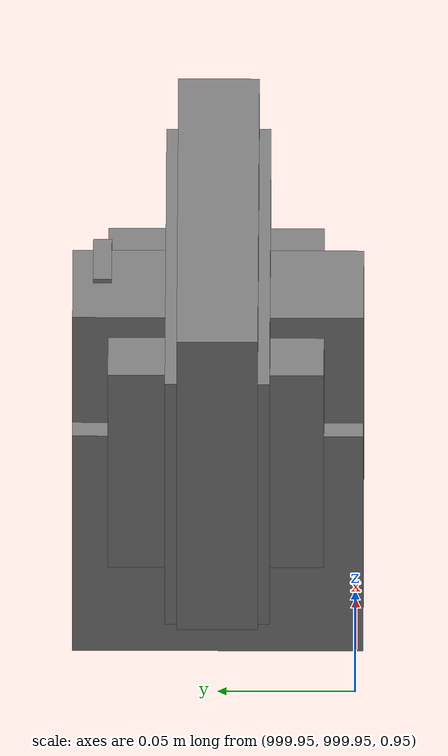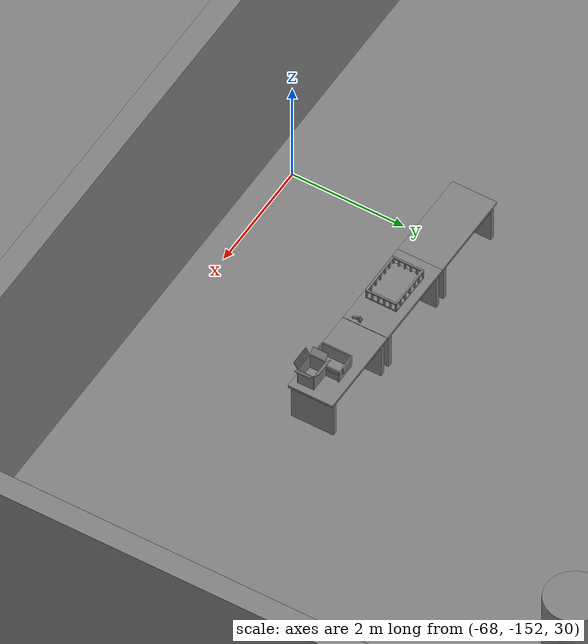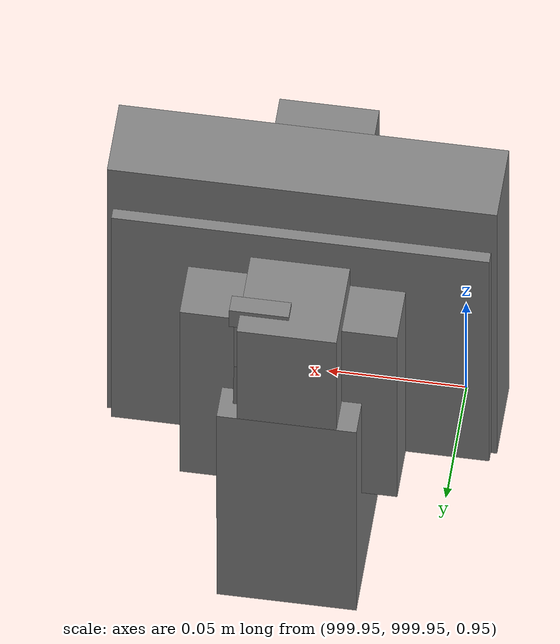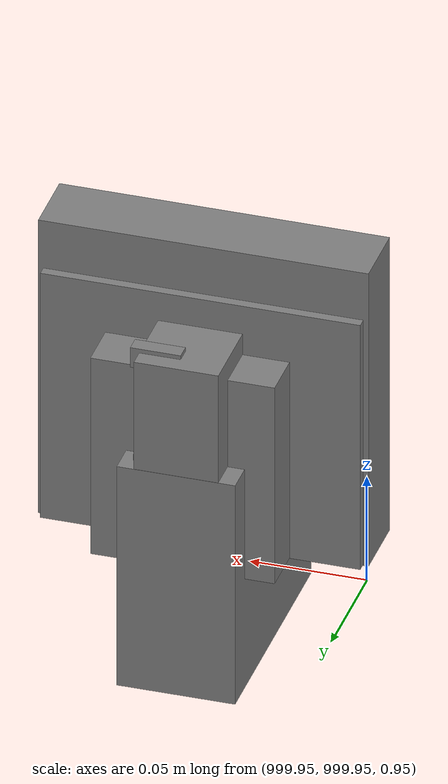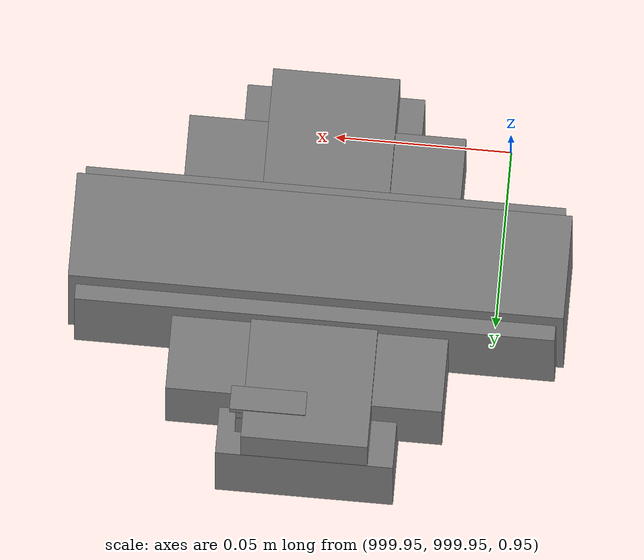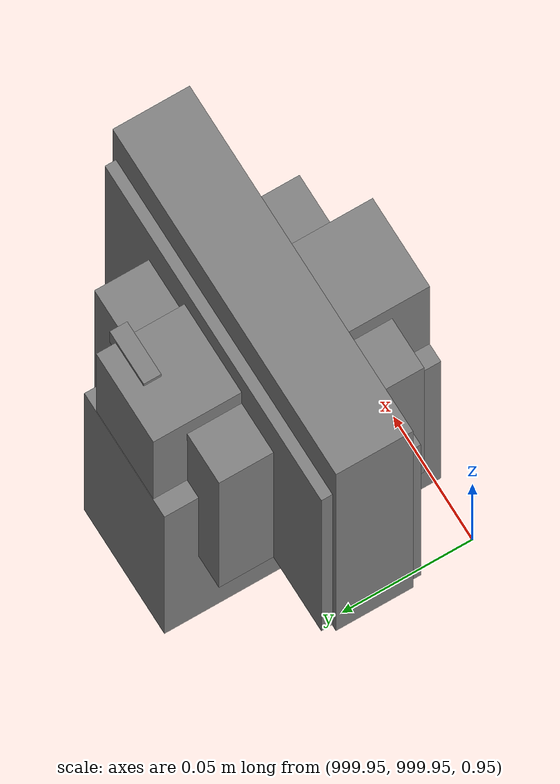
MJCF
<mujoco>
    <option gravity="0.000000000 0.000000000 -9.810000420" timestep="0.0049999999" integrator="implicitfast" density="1.225" viscosity="1.8000001e-05" noslip_iterations="10" iterations="100" sdf_iterations="50">
        <flag multiccd="disable"/>
    </option>
    <size memory="1000M"/>
    <compiler coordinate="local"/>
    <worldbody>
        <light cutoff="30" pos="0 1 1" dir="0 -1 -2"/>
        <light cutoff="30" pos="0 -1 1" dir="0 1 -2"/>
        <body pos="1000.000000000 1000.000000000 1.000000000" euler="0.000011953 0.000005123 -179.999984741" name="openloong_gripper_2f85_fix_base_usda_intel_box">
            <geom contype="1" conaffinity="1" density="1000" type="box" material="" rgba="0.500000000 0.500000000 0.500000000 1.000000000" solimp="0.899999976 0.949999988 0.001000000" friction="1.000000000 0.005000000 0.000100000" solref="0.020000000 1.000000000" margin="0" condim="3" group="0" pos="0.000000000 -0.000067139 0.000082284" quat="0.707106709 0.000000225 0.000000253 0.707106650" size="0.052800003 0.025300000 0.052800003" name="openloong_gripper_2f85_fix_base_usda_geom_291E7B61_1B93_48BA_93B6_7AFBDAEF0980"/>
            <freejoint name="openloong_gripper_2f85_fix_base_usda_intel_box_joint"/>
            <site size="0.005000000 0.005000000 0.005000000" rgba="0.500000000 0.500000000 0.500000000 1.000000000" pos="0.000000000 0.000000000 0.000000000" quat="0.999961913 0.008726500 0.000000000 0.000000000" group="0" type="sphere" name="openloong_gripper_2f85_fix_base_usda_intel_boxsite"/>
        </body>
        <body pos="1000.000000000 999.999938965 1.000000000" euler="0.000000000 0.000000000 180.000000000" name="openloong_gripper_2f85_fix_base_usda_intelcore_i5">
            <geom contype="1" conaffinity="1" density="1000" type="box" material="" rgba="0.500000000 0.500000000 0.500000000 1.000000000" solimp="0.899999976 0.949999988 0.001000000" friction="1.000000000 0.005000000 0.000100000" solref="0.020000000 1.000000000" margin="0" condim="3" group="0" pos="0.000000000 0.000000000 0.051722717" quat="0.707106709 0.000000000 0.000000000 -0.707106769" size="0.052800000 0.018080002 0.052800000" name="openloong_gripper_2f85_fix_base_usda_geom_2CD2682D_1807_4F39_A09E_8B6126FB6346"/>
            <freejoint name="openloong_gripper_2f85_fix_base_usda_intelcore_i5_joint"/>
            <site size="0.005000000 0.005000000 0.005000000" rgba="0.500000000 0.500000000 0.500000000 1.000000000" pos="0.000000000 0.000000000 0.000000000" quat="0.999961913 0.008726534 0.000000000 0.000000000" group="0" type="sphere" name="openloong_gripper_2f85_fix_base_usda_intelcore_i5site"/>
        </body>
        <body pos="-65.889045715 -149.277618408 31.164985657" euler="-124.855140686 -30.484313965 -59.498149872" mocap="true" name="spotlight2_SpotLight"/>
        <body pos="1000.000000000 1000.000000000 1.000000000" euler="0.000000000 0.000000000 180.000000000" name="openloong_gripper_2f85_fix_base_usda_wifi_box">
            <geom contype="1" conaffinity="1" density="1000" type="box" material="" rgba="0.500000000 0.500000000 0.500000000 1.000000000" solimp="0.899999976 0.949999988 0.001000000" friction="1.000000000 0.005000000 0.000100000" solref="0.020000000 1.000000000" margin="0" condim="3" group="0" pos="0.000000000 0.000000000 0.058978677" quat="0.000000000 0.000000047 0.000000000 1.000000000" size="0.068499997 0.018999999 0.059000000" name="openloong_gripper_2f85_fix_base_usda_geom_D864AEFF_1613_4245_8D78_21D75FF59C66"/>
            <freejoint name="openloong_gripper_2f85_fix_base_usda_wifi_box_joint"/>
            <site size="0.005000000 0.005000000 0.005000000" rgba="0.500000000 0.500000000 0.500000000 1.000000000" pos="0.000000000 0.000000000 0.000000000" quat="0.999961913 0.008726500 0.000000000 0.000000000" group="0" type="sphere" name="openloong_gripper_2f85_fix_base_usda_wifi_boxsite"/>
        </body>
        <body pos="1000.000000000 1000.000000000 1.000000000" euler="0.000000000 0.000000000 180.000000000" name="openloong_gripper_2f85_fix_base_usda_cpu_fan">
            <geom contype="1" conaffinity="1" density="1000" type="box" material="" rgba="0.500000000 0.500000000 0.500000000 1.000000000" solimp="0.899999976 0.949999988 0.001000000" friction="1.000000000 0.005000000 0.000100000" solref="0.020000000 1.000000000" margin="0" condim="3" group="0" pos="0.000000000 0.000000000 0.070034981" quat="0.000000000 0.000000000 0.000000000 1.000000000" size="0.070700005 0.014699999 0.070700005" name="openloong_gripper_2f85_fix_base_usda_geom_03088D4B_6058_4802_85AE_946F6DEE8F6A"/>
            <freejoint name="openloong_gripper_2f85_fix_base_usda_cpu_fan_joint"/>
            <site size="0.005000000 0.005000000 0.005000000" rgba="0.500000000 0.500000000 0.500000000 1.000000000" pos="0.000000000 0.000000000 0.000000000" quat="0.999961913 0.008726535 0.000000000 0.000000000" group="0" type="sphere" name="openloong_gripper_2f85_fix_base_usda_cpu_fancsite"/>
        </body>
        <body pos="-66.079269409 -149.266555786 31.168273926" euler="52.934886932 -7.170186996 -150.667678833" mocap="true" name="spotlight3_SpotLight"/>
        <body pos="1000.000000000 1000.000000000 1.000000000" euler="0.000000000 0.000000000 180.000000000" name="openloong_gripper_2f85_fix_base_usda_battery_01">
            <geom contype="1" conaffinity="1" density="1000" type="box" material="" rgba="0.500000000 0.500000000 0.500000000 1.000000000" solimp="0.899999976 0.949999988 0.001000000" friction="1.000000000 0.005000000 0.000100000" solref="0.020000000 1.000000000" margin="0" condim="3" group="0" pos="-0.011123657 -0.041940309 0.101691343" quat="1.000000000 0.000000000 0.000000000 0.000000000" size="0.010800000 0.003375000 0.004725000" name="openloong_gripper_2f85_fix_base_usda_geom_BFCCC494_A9DC_47BA_9D4D_CBFDEBB99313"/>
            <geom contype="1" conaffinity="1" density="1000" type="box" material="" rgba="0.500000000 0.500000000 0.500000000 1.000000000" solimp="0.899999976 0.949999988 0.001000000" friction="1.000000000 0.005000000 0.000100000" solref="0.020000000 1.000000000" margin="0" condim="3" group="0" pos="-0.010876465 -0.044247437 0.047066893" quat="0.998702705 -0.050920475 0.000000000 0.000000000" size="0.009450001 0.002700000 0.024975000" name="openloong_gripper_2f85_fix_base_usda_geom_3A93C01F_9CBD_4C9E_893B_AE4FB9F3DCAC"/>
            <geom contype="1" conaffinity="1" density="1000" type="box" material="" rgba="0.500000000 0.500000000 0.500000000 1.000000000" solimp="0.899999976 0.949999988 0.001000000" friction="1.000000000 0.005000000 0.000100000" solref="0.020000000 1.000000000" margin="0" condim="3" group="0" pos="-0.001235962 -0.000659180 0.047381196" quat="1.000000000 0.000000000 0.000000000 0.000000000" size="0.039420001 0.039150000 0.047250003" name="openloong_gripper_2f85_fix_base_usda_geom_0B8A381D_B412_476F_94CA_FD8C29F61AD4"/>
            <geom contype="1" conaffinity="1" density="1000" type="box" material="" rgba="0.500000000 0.500000000 0.500000000 1.000000000" solimp="0.899999976 0.949999988 0.001000000" friction="1.000000000 0.005000000 0.000100000" solref="0.020000000 1.000000000" margin="0" condim="3" group="0" pos="-0.010876465 -0.039138794 0.009851727" quat="1.000000000 0.000000000 0.000000000 0.000000000" size="0.009450001 0.010800000 0.013500000" name="openloong_gripper_2f85_fix_base_usda_geom_3407E09C_042D_46BB_9030_D105CDD7869C"/>
            <geom contype="1" conaffinity="1" density="1000" type="box" material="" rgba="0.500000000 0.500000000 0.500000000 1.000000000" solimp="0.899999976 0.949999988 0.001000000" friction="1.000000000 0.005000000 0.000100000" solref="0.020000000 1.000000000" margin="0" condim="3" group="0" pos="-0.010876465 -0.041528322 0.071508206" quat="1.000000000 0.000000000 0.000000000 0.000000000" size="0.009450001 0.002700000 0.027000001" name="openloong_gripper_2f85_fix_base_usda_geom_B987B22D_3C38_4382_A274_7C0E8DCA1A53"/>
            <freejoint name="openloong_gripper_2f85_fix_base_usda_battery_01_joint"/>
            <site size="0.005000000 0.005000000 0.005000000" rgba="0.500000000 0.500000000 0.500000000 1.000000000" pos="0.000000000 0.000000000 0.000000000" quat="0.999961913 0.008726500 0.000000000 0.000000000" group="0" type="sphere" name="openloong_gripper_2f85_fix_base_usda_battery_01site"/>
        </body>
        <body pos="-66.061668396 -148.985336304 31.167499542" euler="-133.615219116 83.704162598 29.377079010" mocap="true" name="spotlight4_SpotLight"/>
        <body pos="-64.866622925 -149.383972168 30.183746338" euler="89.999984741 89.999946594 0.000000000" name="openloong_gripper_2f85_fix_base_usda_bluebox_01">
            <geom contype="1" conaffinity="1" density="1000" type="box" material="" rgba="0.500000000 0.500000000 0.500000000 1.000000000" solimp="0.899999976 0.949999988 0.001000000" friction="1.000000000 0.005000000 0.000100000" solref="0.020000000 1.000000000" margin="0" condim="3" group="0" pos="0.276580811 0.187225342 0.000068665" quat="0.707106948 0.000077471 0.707106352 0.000077486" size="0.100000001 0.057999998 0.010000000" name="openloong_gripper_2f85_fix_base_usda_geom_8AEAC4F4_3177_4FFD_BF66_D0358682D679"/>
            <geom contype="1" conaffinity="1" density="1000" type="box" material="" rgba="0.500000000 0.500000000 0.500000000 1.000000000" solimp="0.899999976 0.949999988 0.001000000" friction="1.000000000 0.005000000 0.000100000" solref="0.020000000 1.000000000" margin="0" condim="3" group="0" pos="0.000000000 0.002883911 0.000000000" quat="0.999999881 0.000000000 0.000000000 0.000000000" size="0.254000008 0.003000000 0.172000006" name="openloong_gripper_2f85_fix_base_usda_geom_E110728E_0AC3_4756_9041_561F4012E944"/>
            <geom contype="1" conaffinity="1" density="1000" type="box" material="" rgba="0.500000000 0.500000000 0.500000000 1.000000000" solimp="0.899999976 0.949999988 0.001000000" friction="1.000000000 0.005000000 0.000100000" solref="0.020000000 1.000000000" margin="0" condim="3" group="0" pos="0.000000000 0.124874115 0.173484802" quat="0.999796331 0.020176515 -0.000000015 0.000000030" size="0.259999990 0.119999997 0.007000000" name="openloong_gripper_2f85_fix_base_usda_geom_D94F911D_4288_49FB_BA39_13E9C05471D4"/>
            <geom contype="1" conaffinity="1" density="1000" type="box" material="" rgba="0.500000000 0.500000000 0.500000000 1.000000000" solimp="0.899999976 0.949999988 0.001000000" friction="1.000000000 0.005000000 0.000100000" solref="0.020000000 1.000000000" margin="0" condim="3" group="0" pos="0.000000000 0.124874115 -0.173469543" quat="0.999796331 -0.020176545 -0.000000015 0.000000000" size="0.259999990 0.119999997 0.007000000" name="openloong_gripper_2f85_fix_base_usda_geom_581201AC_F7D1_4630_8557_61149D7D8D61"/>
            <geom contype="1" conaffinity="1" density="1000" type="box" material="" rgba="0.500000000 0.500000000 0.500000000 1.000000000" solimp="0.899999976 0.949999988 0.001000000" friction="1.000000000 0.005000000 0.000100000" solref="0.020000000 1.000000000" margin="0" condim="3" group="0" pos="0.000000000 0.214008331 0.188980103" quat="0.999912977 0.013176724 0.000000015 0.000000000" size="0.259999990 0.029999999 0.012500000" name="openloong_gripper_2f85_fix_base_usda_geom_FBD981F6_4EA4_4D47_AF03_39E7DFB3000D"/>
            <geom contype="1" conaffinity="1" density="1000" type="box" material="" rgba="0.500000000 0.500000000 0.500000000 1.000000000" solimp="0.899999976 0.949999988 0.001000000" friction="1.000000000 0.005000000 0.000100000" solref="0.020000000 1.000000000" margin="0" condim="3" group="0" pos="-0.258361816 0.125289917 0.001876831" quat="0.702796936 -0.020792112 0.710783124 0.020769298" size="0.189999998 0.119999997 0.009000000" name="openloong_gripper_2f85_fix_base_usda_geom_9F6AA4AD_AE45_43F1_9759_64FDC60A317B"/>
            <geom contype="1" conaffinity="1" density="1000" type="box" material="" rgba="0.500000000 0.500000000 0.500000000 1.000000000" solimp="0.899999976 0.949999988 0.001000000" friction="1.000000000 0.005000000 0.000100000" solref="0.020000000 1.000000000" margin="0" condim="3" group="0" pos="0.000000000 0.214008331 -0.188980103" quat="0.999912977 -0.013176769 0.000000030 0.000000015" size="0.259999990 0.029999999 0.012500000" name="openloong_gripper_2f85_fix_base_usda_geom_27AD7137_B6CC_43FD_8C31_B8062561B818"/>
            <geom contype="1" conaffinity="1" density="1000" type="box" material="" rgba="0.500000000 0.500000000 0.500000000 1.000000000" solimp="0.899999976 0.949999988 0.001000000" friction="1.000000000 0.005000000 0.000100000" solref="0.020000000 1.000000000" margin="0" condim="3" group="0" pos="-0.276611328 0.187225342 0.000068665" quat="0.707106650 0.000077441 0.707106709 0.000077456" size="0.100000001 0.057999998 0.010000000" name="openloong_gripper_2f85_fix_base_usda_geom_9B382CA8_F908_468F_9FD8_27B4F4D69B90"/>
            <geom contype="1" conaffinity="1" density="1000" type="box" material="" rgba="0.500000000 0.500000000 0.500000000 1.000000000" solimp="0.899999976 0.949999988 0.001000000" friction="1.000000000 0.005000000 0.000100000" solref="0.020000000 1.000000000" margin="0" condim="3" group="0" pos="0.258331299 0.125289917 0.001876831" quat="0.702851415 0.018856421 0.710823774 -0.019329369" size="0.189999998 0.119999997 0.009000000" name="openloong_gripper_2f85_fix_base_usda_geom_525A85FF_FB74_41AD_B4CF_A465E40DAF59"/>
            <freejoint name="openloong_gripper_2f85_fix_base_usda_bluebox_01_joint"/>
            <site size="0.005000000 0.005000000 0.005000000" rgba="0.500000000 0.500000000 0.500000000 1.000000000" pos="0.000000000 0.000000000 0.000000000" quat="0.999961913 0.008726534 0.000000000 0.000000000" group="0" type="sphere" name="openloong_gripper_2f85_fix_base_usda_bluebox_01site"/>
        </body>
        <body pos="-64.496299744 -149.491867065 30.235729218" euler="0.000000000 0.000000000 89.999946594" name="openloong_gripper_2f85_fix_base_usda_cardboardbox_01">
            <geom contype="1" conaffinity="1" density="1000" type="box" material="" rgba="0.500000000 0.500000000 0.500000000 1.000000000" solimp="0.899999976 0.949999988 0.001000000" friction="1.000000000 0.005000000 0.000100000" solref="0.020000000 1.000000000" margin="0" condim="3" group="0" pos="-0.003166199 -0.004086494 0.005052090" quat="1.000000000 0.000000000 0.000000000 0.000000000" size="0.142499998 0.177500010 0.005000000" name="openloong_gripper_2f85_fix_base_usda_geom_EF2C73C5_9410_4014_A79D_6DA56F4B22A7"/>
            <geom contype="1" conaffinity="1" density="1000" type="box" material="" rgba="0.500000000 0.500000000 0.500000000 1.000000000" solimp="0.899999976 0.949999988 0.001000000" friction="1.000000000 0.005000000 0.000100000" solref="0.020000000 1.000000000" margin="0" condim="3" group="0" pos="-0.003166199 0.170316696 0.150570869" quat="1.000000000 0.000000000 0.000000000 0.000000000" size="0.142499998 0.005000000 0.149999991" name="openloong_gripper_2f85_fix_base_usda_geom_8321155D_E284_4AA0_B7DD_8A0F8CE2B429"/>
            <geom contype="1" conaffinity="1" density="1000" type="box" material="" rgba="0.500000000 0.500000000 0.500000000 1.000000000" solimp="0.899999976 0.949999988 0.001000000" friction="1.000000000 0.005000000 0.000100000" solref="0.020000000 1.000000000" margin="0" condim="3" group="0" pos="-0.147399902 -0.005307198 0.150570869" quat="1.000000000 0.000000000 0.000000000 0.000000000" size="0.005000000 0.177500010 0.149999991" name="openloong_gripper_2f85_fix_base_usda_geom_828E9E16_9068_4ABF_A571_743CFD957AE4"/>
            <geom contype="1" conaffinity="1" density="1000" type="box" material="" rgba="0.500000000 0.500000000 0.500000000 1.000000000" solimp="0.899999976 0.949999988 0.001000000" friction="1.000000000 0.005000000 0.000100000" solref="0.020000000 1.000000000" margin="0" condim="3" group="0" pos="0.140275955 -0.005307198 0.150570869" quat="1.000000000 0.000000000 0.000000000 0.000000000" size="0.005000000 0.177500010 0.149999991" name="openloong_gripper_2f85_fix_base_usda_geom_FACB199F_1E6F_4A2B_9192_78D9579036BC"/>
            <geom contype="1" conaffinity="1" density="1000" type="box" material="" rgba="0.500000000 0.500000000 0.500000000 1.000000000" solimp="0.899999976 0.949999988 0.001000000" friction="1.000000000 0.005000000 0.000100000" solref="0.020000000 1.000000000" margin="0" condim="3" group="0" pos="-0.003166199 -0.181550980 0.150570869" quat="1.000000000 0.000000000 0.000000000 0.000000000" size="0.142499998 0.005000000 0.149999991" name="openloong_gripper_2f85_fix_base_usda_geom_2F7ED679_ED60_40D7_A9BD_BFBC38E6EBD9"/>
            <freejoint name="openloong_gripper_2f85_fix_base_usda_cardboardbox_01_joint"/>
            <site size="0.005000000 0.005000000 0.005000000" rgba="0.500000000 0.500000000 0.500000000 1.000000000" pos="0.000000000 0.000000000 0.000000000" quat="0.999961913 0.008726535 0.000000000 0.000000000" group="0" type="sphere" name="openloong_gripper_2f85_fix_base_usda_site_3A363D96_7C6A_4407_9915_3D2FD8336EC2"/>
            <body pos="0.139160156 -0.004048347 0.301930904" euler="-179.999954224 49.383502960 179.999954224" name="openloong_gripper_2f85_fix_base_usda_A1_006">
                <geom contype="1" conaffinity="1" density="1000" type="box" material="" rgba="0.500000000 0.500000000 0.500000000 1.000000000" solimp="0.899999976 0.949999988 0.001000000" friction="1.000000000 0.005000000 0.000100000" solref="0.020000000 1.000000000" margin="0" condim="3" group="0" pos="-0.071587563 0.000009537 0.001745224" quat="0.999999881 0.000000000 0.000000000 0.000000000" size="0.071249999 0.179999992 0.002500000" name="openloong_gripper_2f85_fix_base_usda_geom_FF7521D2_9DC2_479A_8823_A88767B6E2A2"/>
                <joint armature="0" stiffness="0.07" damping="0.0099999998" axis="0.000000 1.000000 0.000000" type="hinge" name="openloong_gripper_2f85_fix_base_usda_A1_006"/>
            </body>
            <body pos="-0.145902634 -0.004086494 0.301938057" euler="-180.000000000 -60.000011444 -180.000000000" name="openloong_gripper_2f85_fix_base_usda_A2_006">
                <geom contype="1" conaffinity="1" density="1000" type="box" material="" rgba="0.500000000 0.500000000 0.500000000 1.000000000" solimp="0.899999976 0.949999988 0.001000000" friction="1.000000000 0.005000000 0.000100000" solref="0.020000000 1.000000000" margin="0" condim="3" group="0" pos="0.071268082 0.000009537 0.002717972" quat="0.000002921 0.000000000 -0.000000030 0.999999881" size="0.071249999 0.179999992 0.002500000" name="openloong_gripper_2f85_fix_base_usda_geom_B48E360F_F9C2_45B9_BA92_4A9CAEC8B3C6"/>
                <joint armature="0" stiffness="0.07" damping="0.0099999998" axis="0.000000 1.000000 0.000000" type="hinge" name="openloong_gripper_2f85_fix_base_usda_A2_006"/>
            </body>
            <body pos="-0.003385544 0.175991058 0.301930904" euler="-125.858116150 -0.000004561 0.000002331" name="openloong_gripper_2f85_fix_base_usda_B2_006">
                <geom contype="1" conaffinity="1" density="1000" type="box" material="" rgba="0.500000000 0.500000000 0.500000000 1.000000000" solimp="0.899999976 0.949999988 0.001000000" friction="1.000000000 0.005000000 0.000100000" solref="0.020000000 1.000000000" margin="0" condim="3" group="0" pos="0.000009537 -0.070939064 -0.002470016" quat="0.999614120 0.027776197 -0.000000015 0.000000030" size="0.137500003 0.064999998 0.005000000" name="openloong_gripper_2f85_fix_base_usda_geom_AB32E393_74FC_441E_B3BD_471098EB8E41"/>
                <joint armature="0" stiffness="0.07" damping="0.0099999998" axis="1.000000 0.000000 0.000000" type="hinge" name="openloong_gripper_2f85_fix_base_usda_B2_006"/>
            </body>
            <body pos="-0.003385544 -0.184140205 0.301938057" euler="147.805557251 0.000000000 0.000000000" name="openloong_gripper_2f85_fix_base_usda_B1_006">
                <geom contype="1" conaffinity="1" density="1000" type="box" material="" rgba="0.500000000 0.500000000 0.500000000 1.000000000" solimp="0.899999976 0.949999988 0.001000000" friction="1.000000000 0.005000000 0.000100000" solref="0.020000000 1.000000000" margin="0" condim="3" group="0" pos="-0.000028610 0.070202351 -0.002703667" quat="0.999614179 -0.027776167 0.000000000 0.000000000" size="0.137500003 0.064999998 0.005000000" name="openloong_gripper_2f85_fix_base_usda_geom_48A5C1AE_8CAD_40E1_AF13_E5083E16E11B"/>
                <joint armature="0" stiffness="0.07" damping="0.0099999998" axis="1.000000 0.000000 0.000000" type="hinge" name="openloong_gripper_2f85_fix_base_usda_B1_006"/>
            </body>
        </body>
        <body pos="-65.882858276 -149.481979370 30.229999542" euler="-64.487716675 0.000000000 0.000000000" name="openloong_gripper_2f85_fix_base_usda_Barcode">
            <geom contype="1" conaffinity="1" density="1000" type="box" material="" rgba="0.500000000 0.500000000 0.500000000 1.000000000" solimp="0.899999976 0.949999988 0.001000000" friction="1.000000000 0.005000000 0.000100000" solref="0.020000000 1.000000000" margin="0" condim="3" group="0" pos="0.000000000 0.013038635 0.001419067" quat="0.000000000 0.000000000 0.000000000 1.000000119" size="0.034000002 0.010000000 0.017999999" name="openloong_gripper_2f85_fix_base_usda_geom_96C6695B_D425_4F34_9E06_1AC9DC66C8BB"/>
            <geom contype="1" conaffinity="1" density="1000" type="box" material="" rgba="0.500000000 0.500000000 0.500000000 1.000000000" solimp="0.899999976 0.949999988 0.001000000" friction="1.000000000 0.005000000 0.000100000" solref="0.020000000 1.000000000" margin="0" condim="3" group="0" pos="0.000000000 -0.035301208 -0.007095337" quat="0.000000000 0.000000000 -0.043619365 0.999048233" size="0.028999999 0.010000000 0.020000000" name="openloong_gripper_2f85_fix_base_usda_geom_A824E03E_2982_40A4_99EA_03535C19B45F"/>
            <geom contype="1" conaffinity="1" density="1000" type="box" material="" rgba="0.500000000 0.500000000 0.500000000 1.000000000" solimp="0.899999976 0.949999988 0.001000000" friction="1.000000000 0.005000000 0.000100000" solref="0.020000000 1.000000000" margin="0" condim="3" group="0" pos="0.000000000 -0.043411255 -0.011749268" quat="0.922262907 0.386563420 0.000000000 0.000000000" size="0.026000001 0.010000000 0.020000000" name="openloong_gripper_2f85_fix_base_usda_geom_14C66464_44F3_436D_95A2_544A431811D3"/>
            <geom contype="1" conaffinity="1" density="1000" type="box" material="" rgba="0.500000000 0.500000000 0.500000000 1.000000000" solimp="0.899999976 0.949999988 0.001000000" friction="1.000000000 0.005000000 0.000100000" solref="0.020000000 1.000000000" margin="0" condim="3" group="0" pos="0.000000000 -0.016967773 -0.031860352" quat="0.000000000 0.000000000 0.000000000 1.000000119" size="0.008000000 0.010000000 0.013000000" name="openloong_gripper_2f85_fix_base_usda_geom_6C692A0E_F0BB_4C75_8033_22F83657F7E5"/>
            <geom contype="1" conaffinity="1" density="1000" type="box" material="" rgba="0.500000000 0.500000000 0.500000000 1.000000000" solimp="0.899999976 0.949999988 0.001000000" friction="1.000000000 0.005000000 0.000100000" solref="0.020000000 1.000000000" margin="0" condim="3" group="0" pos="0.000000000 -0.001869202 0.000312805" quat="0.953716993 0.300705761 0.000000000 0.000000000" size="0.032000002 0.010000000 0.018999999" name="openloong_gripper_2f85_fix_base_usda_geom_82ED0084_6D67_4D3C_A87A_5BC89FF0A808"/>
            <geom contype="1" conaffinity="1" density="1000" type="box" material="" rgba="0.500000000 0.500000000 0.500000000 1.000000000" solimp="0.899999976 0.949999988 0.001000000" friction="1.000000000 0.005000000 0.000100000" solref="0.020000000 1.000000000" margin="0" condim="3" group="0" pos="0.000000000 -0.019531250 -0.003173828" quat="0.953716993 0.300705761 0.000000000 0.000000000" size="0.030999999 0.010000000 0.020000000" name="openloong_gripper_2f85_fix_base_usda_geom_997CC06C_7821_43A2_A421_A2AFDA1CD5AA"/>
            <geom contype="1" conaffinity="1" density="1000" type="box" material="" rgba="0.500000000 0.500000000 0.500000000 1.000000000" solimp="0.899999976 0.949999988 0.001000000" friction="1.000000000 0.005000000 0.000100000" solref="0.020000000 1.000000000" margin="0" condim="3" group="0" pos="0.000000000 -0.035301208 -0.007095337" quat="0.953716993 0.300705761 0.000000000 0.000000000" size="0.028999999 0.010000000 0.020000000" name="openloong_gripper_2f85_fix_base_usda_geom_CDB9F831_0D61_4742_80F2_E1C360351F05"/>
            <geom contype="1" conaffinity="1" density="1000" type="box" material="" rgba="0.500000000 0.500000000 0.500000000 1.000000000" solimp="0.899999976 0.949999988 0.001000000" friction="1.000000000 0.005000000 0.000100000" solref="0.020000000 1.000000000" margin="0" condim="3" group="0" pos="0.000000000 -0.042617798 -0.071121216" quat="0.000000000 0.000000000 0.000000000 1.000000119" size="0.013000000 0.021000000 0.059999999" name="openloong_gripper_2f85_fix_base_usda_geom_992F4EFE_7D4B_4E44_A03D_93D20F6BE02E"/>
            <freejoint name="openloong_gripper_2f85_fix_base_usda_Barcode_joint"/>
            <site size="0.005000000 0.005000000 0.005000000" rgba="0.500000000 0.500000000 0.500000000 1.000000000" pos="0.000000000 0.000000000 0.000000000" quat="1.000000000 0.000000000 0.000000000 0.000000000" group="0" type="sphere" name="openloong_gripper_2f85_fix_base_usda_Barcode_site"/>
        </body>
        <body pos="-66.745018005 -149.392349243 30.184000015" euler="0.000000000 0.000000000 89.999946594" name="[22332873096886]_Basket_01">
            <geom contype="1" conaffinity="1" density="1000" type="box" material="" rgba="0.500000000 0.500000000 0.500000000 1.000000000" solimp="0.899999976 0.949999988 0.001000000" friction="1.000000000 0.005000000 0.000100000" solref="0.020000000 1.000000000" margin="0" condim="3" group="0" pos="-0.052425385 0.389207840 0.089787483" quat="0.707107008 0.000000000 0.000000000 0.707106411" size="0.014249999 0.014249999 0.059999999" name="[22332873096886]_geom_C52192D9_8974_4177_8B15_BA9D35190B98"/>
            <geom contype="1" conaffinity="1" density="1000" type="box" material="" rgba="0.500000000 0.500000000 0.500000000 1.000000000" solimp="0.899999976 0.949999988 0.001000000" friction="1.000000000 0.005000000 0.000100000" solref="0.020000000 1.000000000" margin="0" condim="3" group="0" pos="0.264015198 -0.133043289 0.089787483" quat="0.707107008 0.000000000 0.000000000 0.707106411" size="0.014249999 0.014249999 0.059999999" name="[22332873096886]_geom_D72DA8AC_AD22_4450_BC3A_ED4E5851417A"/>
            <geom contype="1" conaffinity="1" density="1000" type="box" material="" rgba="0.500000000 0.500000000 0.500000000 1.000000000" solimp="0.899999976 0.949999988 0.001000000" friction="1.000000000 0.005000000 0.000100000" solref="0.020000000 1.000000000" margin="0" condim="3" group="0" pos="-0.264015198 -0.265548706 0.089793205" quat="0.707107008 0.000000000 0.000000000 0.707106411" size="0.014249999 0.014249999 0.059999999" name="[22332873096886]_geom_795F5105_33BB_405F_9B85_AC7DF6E63C76"/>
            <geom contype="1" conaffinity="1" density="1000" type="box" material="" rgba="0.500000000 0.500000000 0.500000000 1.000000000" solimp="0.899999976 0.949999988 0.001000000" friction="1.000000000 0.005000000 0.000100000" solref="0.020000000 1.000000000" margin="0" condim="3" group="0" pos="-0.160263062 -0.389322281 0.089793205" quat="0.707107008 0.000000000 0.000000000 0.707106411" size="0.014249999 0.014249999 0.059999999" name="[22332873096886]_geom_9853A417_2DB4_482C_8F4B_9C1CBCB4E127"/>
            <geom contype="1" conaffinity="1" density="1000" type="box" material="" rgba="0.500000000 0.500000000 0.500000000 1.000000000" solimp="0.899999976 0.949999988 0.001000000" friction="1.000000000 0.005000000 0.000100000" solref="0.020000000 1.000000000" margin="0" condim="3" group="0" pos="0.162265778 -0.389322281 0.089787483" quat="0.707107008 0.000000000 0.000000000 0.707106411" size="0.014249999 0.014249999 0.059999999" name="[22332873096886]_geom_E83C24BC_BC72_4019_BCA8_6BF7562A5711"/>
            <geom contype="1" conaffinity="1" density="1000" type="box" material="" rgba="0.500000000 0.500000000 0.500000000 1.000000000" solimp="0.899999976 0.949999988 0.001000000" friction="1.000000000 0.005000000 0.000100000" solref="0.020000000 1.000000000" margin="0" condim="3" group="0" pos="0.264015198 0.389207840 0.089787483" quat="0.707107008 0.000000000 0.000000000 0.707106411" size="0.014249999 0.014249999 0.059999999" name="[22332873096886]_geom_6E545DF0_2CB7_42E7_9470_78A74F772F61"/>
            <geom contype="1" conaffinity="1" density="1000" type="box" material="" rgba="0.500000000 0.500000000 0.500000000 1.000000000" solimp="0.899999976 0.949999988 0.001000000" friction="1.000000000 0.005000000 0.000100000" solref="0.020000000 1.000000000" margin="0" condim="3" group="0" pos="-0.264015198 -0.133043289 0.089793205" quat="0.707107008 0.000000000 0.000000000 0.707106411" size="0.014249999 0.014249999 0.059999999" name="[22332873096886]_geom_A08ABFCD_889E_4790_A8CE_A7A4A4D36D10"/>
            <geom contype="1" conaffinity="1" density="1000" type="box" material="" rgba="0.500000000 0.500000000 0.500000000 1.000000000" solimp="0.899999976 0.949999988 0.001000000" friction="1.000000000 0.005000000 0.000100000" solref="0.020000000 1.000000000" margin="0" condim="3" group="0" pos="-0.264026642 0.269256592 0.089793205" quat="0.707107008 0.000000000 0.000000000 0.707106411" size="0.014249999 0.014249999 0.059999999" name="[22332873096886]_geom_EE6949A9_4A3C_4673_9862_38A47B7785F0"/>
            <geom contype="1" conaffinity="1" density="1000" type="box" material="" rgba="0.500000000 0.500000000 0.500000000 1.000000000" solimp="0.899999976 0.949999988 0.001000000" friction="1.000000000 0.005000000 0.000100000" solref="0.020000000 1.000000000" margin="0" condim="3" group="0" pos="0.054462433 0.389207840 0.089787483" quat="0.707107008 0.000000000 0.000000000 0.707106411" size="0.014249999 0.014249999 0.059999999" name="[22332873096886]_geom_1F0B97E7_859F_4B67_8A41_1C98EF5785E5"/>
            <geom contype="1" conaffinity="1" density="1000" type="box" material="" rgba="0.500000000 0.500000000 0.500000000 1.000000000" solimp="0.899999976 0.949999988 0.001000000" friction="1.000000000 0.005000000 0.000100000" solref="0.020000000 1.000000000" margin="0" condim="3" group="0" pos="0.054462433 -0.389322281 0.089787483" quat="0.707107008 0.000000000 0.000000000 0.707106411" size="0.014249999 0.014249999 0.059999999" name="[22332873096886]_geom_DF716F19_F418_4538_A921_51E760A6009B"/>
            <geom contype="1" conaffinity="1" density="1000" type="box" material="" rgba="0.500000000 0.500000000 0.500000000 1.000000000" solimp="0.899999976 0.949999988 0.001000000" friction="1.000000000 0.005000000 0.000100000" solref="0.020000000 1.000000000" margin="0" condim="3" group="0" pos="0.264015198 0.269256592 0.089793205" quat="0.707107008 0.000000000 0.000000000 0.707106411" size="0.014249999 0.014249999 0.059999999" name="[22332873096886]_geom_F0812F59_B630_436D_B52E_4F1F3C706850"/>
            <geom contype="1" conaffinity="1" density="1000" type="box" material="" rgba="0.500000000 0.500000000 0.500000000 1.000000000" solimp="0.899999976 0.949999988 0.001000000" friction="1.000000000 0.005000000 0.000100000" solref="0.020000000 1.000000000" margin="0" condim="3" group="0" pos="0.264015198 -0.389322281 0.089787483" quat="0.707107008 0.000000000 0.000000000 0.707106411" size="0.014249999 0.014249999 0.059999999" name="[22332873096886]_geom_15CE61DC_0FEB_42B4_946D_2AB9A14291C5"/>
            <geom contype="1" conaffinity="1" density="1000" type="box" material="" rgba="0.500000000 0.500000000 0.500000000 1.000000000" solimp="0.899999976 0.949999988 0.001000000" friction="1.000000000 0.005000000 0.000100000" solref="0.020000000 1.000000000" margin="0" condim="3" group="0" pos="0.000000000 0.000000000 0.015998840" quat="0.707107008 0.000000000 0.000000000 0.707106411" size="0.403499991 0.279000014 0.015750000" name="[22332873096886]_geom_E352F690_A883_402C_B4D8_7386EFE9783C"/>
            <geom contype="1" conaffinity="1" density="1000" type="box" material="" rgba="0.500000000 0.500000000 0.500000000 1.000000000" solimp="0.899999976 0.949999988 0.001000000" friction="1.000000000 0.005000000 0.000100000" solref="0.020000000 1.000000000" margin="0" condim="3" group="0" pos="0.000000000 -0.389476776 0.163619041" quat="0.707107008 0.000000000 0.000000000 0.707106411" size="0.015000000 0.277500004 0.015750000" name="[22332873096886]_geom_D32DF11B_3C30_4247_BF09_8D7028DE1972"/>
            <geom contype="1" conaffinity="1" density="1000" type="box" material="" rgba="0.500000000 0.500000000 0.500000000 1.000000000" solimp="0.899999976 0.949999988 0.001000000" friction="1.000000000 0.005000000 0.000100000" solref="0.020000000 1.000000000" margin="0" condim="3" group="0" pos="0.162265778 0.389207840 0.089787483" quat="0.707107008 0.000000000 0.000000000 0.707106411" size="0.014249999 0.014249999 0.059999999" name="[22332873096886]_geom_34BF68A4_4281_429E_A484_04970940994F"/>
            <geom contype="1" conaffinity="1" density="1000" type="box" material="" rgba="0.500000000 0.500000000 0.500000000 1.000000000" solimp="0.899999976 0.949999988 0.001000000" friction="1.000000000 0.005000000 0.000100000" solref="0.020000000 1.000000000" margin="0" condim="3" group="0" pos="0.000000000 0.389471054 0.163619041" quat="0.707107008 0.000000000 0.000000000 0.707106411" size="0.015000000 0.277500004 0.015750000" name="[22332873096886]_geom_989A4B4B_20CE_49FC_BC0B_2F0DB9E1D150"/>
            <geom contype="1" conaffinity="1" density="1000" type="box" material="" rgba="0.500000000 0.500000000 0.500000000 1.000000000" solimp="0.899999976 0.949999988 0.001000000" friction="1.000000000 0.005000000 0.000100000" solref="0.020000000 1.000000000" margin="0" condim="3" group="0" pos="-0.263511658 0.000000000 0.163619041" quat="0.707107008 0.000000000 0.000000000 0.707106411" size="0.403499991 0.015000000 0.015750000" name="[22332873096886]_geom_56C11275_9D84_44D0_979D_4B8E29AD3773"/>
            <geom contype="1" conaffinity="1" density="1000" type="box" material="" rgba="0.500000000 0.500000000 0.500000000 1.000000000" solimp="0.899999976 0.949999988 0.001000000" friction="1.000000000 0.005000000 0.000100000" solref="0.020000000 1.000000000" margin="0" condim="3" group="0" pos="-0.264015198 0.141334534 0.089793205" quat="0.707107008 0.000000000 0.000000000 0.707106411" size="0.014249999 0.014249999 0.059999999" name="[22332873096886]_geom_9D91835B_9EF4_4583_A396_FDA1E63CC44F"/>
            <geom contype="1" conaffinity="1" density="1000" type="box" material="" rgba="0.500000000 0.500000000 0.500000000 1.000000000" solimp="0.899999976 0.949999988 0.001000000" friction="1.000000000 0.005000000 0.000100000" solref="0.020000000 1.000000000" margin="0" condim="3" group="0" pos="0.264015198 -0.265548706 0.089787483" quat="0.707107008 0.000000000 0.000000000 0.707106411" size="0.014249999 0.014249999 0.059999999" name="[22332873096886]_geom_60351E18_5B29_4E2C_ACF9_EDEC233666D2"/>
            <geom contype="1" conaffinity="1" density="1000" type="box" material="" rgba="0.500000000 0.500000000 0.500000000 1.000000000" solimp="0.899999976 0.949999988 0.001000000" friction="1.000000000 0.005000000 0.000100000" solref="0.020000000 1.000000000" margin="0" condim="3" group="0" pos="-0.160263062 0.389207840 0.089787483" quat="0.707107008 0.000000000 0.000000000 0.707106411" size="0.014249999 0.014249999 0.059999999" name="[22332873096886]_geom_273CE08B_4C59_4476_AB8E_7ACD39AC83D6"/>
            <geom contype="1" conaffinity="1" density="1000" type="box" material="" rgba="0.500000000 0.500000000 0.500000000 1.000000000" solimp="0.899999976 0.949999988 0.001000000" friction="1.000000000 0.005000000 0.000100000" solref="0.020000000 1.000000000" margin="0" condim="3" group="0" pos="-0.052425385 -0.389322281 0.089787483" quat="0.707107008 0.000000000 0.000000000 0.707106411" size="0.014249999 0.014249999 0.059999999" name="[22332873096886]_geom_DFA6440B_8A9E_4D41_8DEE_2E5EF58E0E43"/>
            <geom contype="1" conaffinity="1" density="1000" type="box" material="" rgba="0.500000000 0.500000000 0.500000000 1.000000000" solimp="0.899999976 0.949999988 0.001000000" friction="1.000000000 0.005000000 0.000100000" solref="0.020000000 1.000000000" margin="0" condim="3" group="0" pos="-0.264026642 -0.389322281 0.089793205" quat="0.707107008 0.000000000 0.000000000 0.707106411" size="0.014249999 0.014249999 0.059999999" name="[22332873096886]_geom_05DF3C9F_07F9_411F_A0AA_686B78322EAD"/>
            <geom contype="1" conaffinity="1" density="1000" type="box" material="" rgba="0.500000000 0.500000000 0.500000000 1.000000000" solimp="0.899999976 0.949999988 0.001000000" friction="1.000000000 0.005000000 0.000100000" solref="0.020000000 1.000000000" margin="0" condim="3" group="0" pos="0.264015198 0.141334534 0.089787483" quat="0.707107008 0.000000000 0.000000000 0.707106411" size="0.014249999 0.014249999 0.059999999" name="[22332873096886]_geom_1F58706B_D117_4D2E_989C_F3AF81F1FFAA"/>
            <geom contype="1" conaffinity="1" density="1000" type="box" material="" rgba="0.500000000 0.500000000 0.500000000 1.000000000" solimp="0.899999976 0.949999988 0.001000000" friction="1.000000000 0.005000000 0.000100000" solref="0.020000000 1.000000000" margin="0" condim="3" group="0" pos="-0.264015198 0.389207840 0.089793205" quat="0.707107008 0.000000000 0.000000000 0.707106411" size="0.014249999 0.014249999 0.059999999" name="[22332873096886]_geom_8BEDE9C6_226A_4E92_A969_2A62A43636FD"/>
            <geom contype="1" conaffinity="1" density="1000" type="box" material="" rgba="0.500000000 0.500000000 0.500000000 1.000000000" solimp="0.899999976 0.949999988 0.001000000" friction="1.000000000 0.005000000 0.000100000" solref="0.020000000 1.000000000" margin="0" condim="3" group="0" pos="0.264015198 0.004480362 0.089787483" quat="0.707107008 0.000000000 0.000000000 0.707106411" size="0.014249999 0.014249999 0.059999999" name="[22332873096886]_geom_550DFCB0_4FA2_4273_8E65_999291F9865C"/>
            <geom contype="1" conaffinity="1" density="1000" type="box" material="" rgba="0.500000000 0.500000000 0.500000000 1.000000000" solimp="0.899999976 0.949999988 0.001000000" friction="1.000000000 0.005000000 0.000100000" solref="0.020000000 1.000000000" margin="0" condim="3" group="0" pos="0.263694763 -0.000011444 0.163619041" quat="0.707107008 0.000000000 0.000000000 0.707106411" size="0.403499991 0.015000000 0.015750000" name="[22332873096886]_geom_D1B7033A_8342_417C_BD76_B507BC0E9F90"/>
            <geom contype="1" conaffinity="1" density="1000" type="box" material="" rgba="0.500000000 0.500000000 0.500000000 1.000000000" solimp="0.899999976 0.949999988 0.001000000" friction="1.000000000 0.005000000 0.000100000" solref="0.020000000 1.000000000" margin="0" condim="3" group="0" pos="-0.264015198 0.004480362 0.089793205" quat="0.707107008 0.000000000 0.000000000 0.707106411" size="0.014249999 0.014249999 0.059999999" name="[22332873096886]_geom_9D6C2D18_42BC_4609_A11A_C2B480EABDDE"/>
            <freejoint name="[22332873096886]_joint_C998C91F_A3AA_4C81_A1F9_FD1AA8D2605C"/>
        </body>
        <body pos="0.000000000 0.000000000 0.000000000" euler="0.000000000 0.000000000 0.000000000" name="Static Objects_Static Objects">
            <geom contype="1" conaffinity="1" density="1000" type="box" material="" rgba="0.500000000 0.500000000 0.500000000 1.000000000" solimp="0.899999976 0.949999988 0.001000000" friction="1.000000000 0.005000000 0.000100000" solref="0.020000000 1.000000000" margin="0" condim="3" group="0" pos="-67.544113159 -149.365814209 29.727830887" quat="0.500000417 0.499999970 0.499999553 0.499999970" size="0.381000012 0.319999993 0.041000001" name="Static Objects_geom_271A79A6_FFD5_442C_821E_029B0922A6EC"/>
            <geom contype="1" conaffinity="1" density="1000" type="box" material="" rgba="0.500000000 0.500000000 0.500000000 1.000000000" solimp="0.899999976 0.949999988 0.001000000" friction="1.000000000 0.005000000 0.000100000" solref="0.020000000 1.000000000" margin="0" condim="3" group="0" pos="-68.239501953 -149.365814209 30.086868286" quat="0.500000417 0.499999970 0.499999553 0.499999970" size="0.370999992 0.039500002 0.745000005" name="Static Objects_geom_D20912D0_A6ED_41E6_BC19_66FD8CCB4713"/>
            <geom contype="1" conaffinity="1" density="1000" type="box" material="" rgba="0.500000000 0.500000000 0.500000000 1.000000000" solimp="0.899999976 0.949999988 0.001000000" friction="1.000000000 0.005000000 0.000100000" solref="0.020000000 1.000000000" margin="0" condim="3" group="0" pos="-68.239501953 -149.365814209 30.147235870" quat="0.500000417 0.499999970 0.499999553 0.499999970" size="0.400000006 0.022000000 0.800000012" name="Static Objects_geom_838FDEA2_9E51_4585_A136_9ADD3307DF40"/>
            <geom contype="1" conaffinity="1" density="1000" type="box" material="" rgba="0.500000000 0.500000000 0.500000000 1.000000000" solimp="0.899999976 0.949999988 0.001000000" friction="1.000000000 0.005000000 0.000100000" solref="0.020000000 1.000000000" margin="0" condim="3" group="0" pos="-68.934890747 -149.365814209 29.727830887" quat="0.500000417 0.499999970 0.499999553 0.499999970" size="0.381000012 0.319999993 0.041000001" name="Static Objects_geom_44C6A431_BAFF_4920_8C18_0EAEEF47572A"/>
            <geom contype="1" conaffinity="1" density="1000" type="box" material="" rgba="0.500000000 0.500000000 0.500000000 1.000000000" solimp="0.899999976 0.949999988 0.001000000" friction="1.000000000 0.005000000 0.000100000" solref="0.020000000 1.000000000" margin="0" condim="3" group="0" pos="-68.239501953 -149.365814209 29.561563492" quat="0.500000417 0.499999970 0.499999553 0.499999970" size="0.020000000 0.022000000 0.660000026" name="Static Objects_geom_A2D32288_8E91_4F04_8227_0DA7B332A02E"/>
            <geom contype="1" conaffinity="1" density="1000" type="box" material="" rgba="0.500000000 0.500000000 0.500000000 1.000000000" solimp="0.899999976 0.949999988 0.001000000" friction="1.000000000 0.005000000 0.000100000" solref="0.020000000 1.000000000" margin="0" condim="3" group="0" pos="-65.945671082 -149.365814209 29.727830887" quat="0.500000417 0.499999970 0.499999553 0.499999970" size="0.381000012 0.319999993 0.041000001" name="Static Objects_geom_6DA2E5FA_64BE_480A_A0DE_823B4E1C98CB"/>
            <geom contype="1" conaffinity="1" density="1000" type="box" material="" rgba="0.500000000 0.500000000 0.500000000 1.000000000" solimp="0.899999976 0.949999988 0.001000000" friction="1.000000000 0.005000000 0.000100000" solref="0.020000000 1.000000000" margin="0" condim="3" group="0" pos="-66.641059875 -149.365814209 30.086868286" quat="0.500000417 0.499999970 0.499999553 0.499999970" size="0.370999992 0.039500002 0.745000005" name="Static Objects_geom_6FB94C51_2EC8_4861_8222_F7298F26A656"/>
            <geom contype="1" conaffinity="1" density="1000" type="box" material="" rgba="0.500000000 0.500000000 0.500000000 1.000000000" solimp="0.899999976 0.949999988 0.001000000" friction="1.000000000 0.005000000 0.000100000" solref="0.020000000 1.000000000" margin="0" condim="3" group="0" pos="-66.641059875 -149.365814209 30.147235870" quat="0.500000417 0.499999970 0.499999553 0.499999970" size="0.400000006 0.022000000 0.800000012" name="Static Objects_geom_59D87D8E_3F4C_403F_8B9C_EAF8ACF10180"/>
            <geom contype="1" conaffinity="1" density="1000" type="box" material="" rgba="0.500000000 0.500000000 0.500000000 1.000000000" solimp="0.899999976 0.949999988 0.001000000" friction="1.000000000 0.005000000 0.000100000" solref="0.020000000 1.000000000" margin="0" condim="3" group="0" pos="-67.336448669 -149.365814209 29.727830887" quat="0.500000417 0.499999970 0.499999553 0.499999970" size="0.381000012 0.319999993 0.041000001" name="Static Objects_geom_60B5BE27_EBAD_4CA8_9F7A_4D7C990EDE5E"/>
            <geom contype="1" conaffinity="1" density="1000" type="box" material="" rgba="0.500000000 0.500000000 0.500000000 1.000000000" solimp="0.899999976 0.949999988 0.001000000" friction="1.000000000 0.005000000 0.000100000" solref="0.020000000 1.000000000" margin="0" condim="3" group="0" pos="-66.641059875 -149.365814209 29.561563492" quat="0.500000417 0.499999970 0.499999553 0.499999970" size="0.020000000 0.022000000 0.660000026" name="Static Objects_geom_0AF5B229_813A_46D2_B1C7_1B33F5881755"/>
            <geom contype="1" conaffinity="1" density="1000" type="box" material="" rgba="0.500000000 0.500000000 0.500000000 1.000000000" solimp="0.899999976 0.949999988 0.001000000" friction="1.000000000 0.005000000 0.000100000" solref="0.020000000 1.000000000" margin="0" condim="3" group="0" pos="-64.338577271 -149.365814209 29.727830887" quat="0.500000417 0.499999970 0.499999553 0.499999970" size="0.381000012 0.319999993 0.041000001" name="Static Objects_geom_5C3941D4_06D2_4CC6_AAC5_8ABD815D3404"/>
            <geom contype="1" conaffinity="1" density="1000" type="box" material="" rgba="0.500000000 0.500000000 0.500000000 1.000000000" solimp="0.899999976 0.949999988 0.001000000" friction="1.000000000 0.005000000 0.000100000" solref="0.020000000 1.000000000" margin="0" condim="3" group="0" pos="-65.033966064 -149.365814209 30.086868286" quat="0.500000417 0.499999970 0.499999553 0.499999970" size="0.370999992 0.039500002 0.745000005" name="Static Objects_geom_17EB0411_F910_476A_91A3_0FA5B464A3B1"/>
            <geom contype="1" conaffinity="1" density="1000" type="box" material="" rgba="0.500000000 0.500000000 0.500000000 1.000000000" solimp="0.899999976 0.949999988 0.001000000" friction="1.000000000 0.005000000 0.000100000" solref="0.020000000 1.000000000" margin="0" condim="3" group="0" pos="-65.033966064 -149.365814209 30.147235870" quat="0.500000417 0.499999970 0.499999553 0.499999970" size="0.400000006 0.022000000 0.800000012" name="Static Objects_geom_46D80BD4_F470_4ECA_8190_EDE3582586F1"/>
            <geom contype="1" conaffinity="1" density="1000" type="box" material="" rgba="0.500000000 0.500000000 0.500000000 1.000000000" solimp="0.899999976 0.949999988 0.001000000" friction="1.000000000 0.005000000 0.000100000" solref="0.020000000 1.000000000" margin="0" condim="3" group="0" pos="-65.729354858 -149.365814209 29.727830887" quat="0.500000417 0.499999970 0.499999553 0.499999970" size="0.381000012 0.319999993 0.041000001" name="Static Objects_geom_6A36712C_7D49_4B66_8261_7DC33FDC1EF1"/>
            <geom contype="1" conaffinity="1" density="1000" type="box" material="" rgba="0.500000000 0.500000000 0.500000000 1.000000000" solimp="0.899999976 0.949999988 0.001000000" friction="1.000000000 0.005000000 0.000100000" solref="0.020000000 1.000000000" margin="0" condim="3" group="0" pos="-65.033966064 -149.365814209 29.561563492" quat="0.500000417 0.499999970 0.499999553 0.499999970" size="0.020000000 0.022000000 0.660000026" name="Static Objects_geom_732C8EE6_91D0_4E4C_B6A6_F68BFC114CCA"/>
            <geom contype="1" conaffinity="1" density="1000" type="box" material="" rgba="0.500000000 0.500000000 0.500000000 1.000000000" solimp="0.899999976 0.949999988 0.001000000" friction="1.000000000 0.005000000 0.000100000" solref="0.020000000 1.000000000" margin="0" condim="3" group="0" pos="-61.754566193 -137.853729248 33.906845093" quat="0.707107067 0.000000000 0.000000000 0.707106471" size="0.759999990 0.759999990 4.500000000" name="Static Objects_geom_F4D52ABA_0B46_4C0E_9AA1_6763C6EC941B"/>
            <geom contype="1" conaffinity="1" density="1000" type="box" material="" rgba="0.500000000 0.500000000 0.500000000 1.000000000" solimp="0.899999976 0.949999988 0.001000000" friction="1.000000000 0.005000000 0.000100000" solref="0.020000000 1.000000000" margin="0" condim="3" group="0" pos="-57.511135101 -144.927108765 31.707921982" quat="1.000000000 0.000000000 0.000000000 0.000000000" size="0.200000003 8.000000000 2.299999952" name="Static Objects_geom_FEF4A963_6B87_4377_9848_895F866C7CBC"/>
            <geom contype="1" conaffinity="1" density="1000" type="box" material="" rgba="0.500000000 0.500000000 0.500000000 1.000000000" solimp="0.899999976 0.949999988 0.001000000" friction="1.000000000 0.005000000 0.000100000" solref="0.020000000 1.000000000" margin="0" condim="3" group="0" pos="-80.517646790 -157.574050903 31.688196182" quat="0.707107067 0.000000000 0.000000000 0.707106471" size="0.600000024 0.600000024 2.299999952" name="Static Objects_geom_8F26BD50_BE49_4AE0_9770_33E03DA9D727"/>
            <geom contype="1" conaffinity="1" density="1000" type="box" material="" rgba="0.500000000 0.500000000 0.500000000 1.000000000" solimp="0.899999976 0.949999988 0.001000000" friction="1.000000000 0.005000000 0.000100000" solref="0.020000000 1.000000000" margin="0" condim="3" group="0" pos="-80.711044312 -147.414932251 31.666158676" quat="1.000000000 0.000000000 0.000000000 0.000000000" size="0.200000003 10.000000000 2.299999952" name="Static Objects_geom_EEA665C9_7AD8_428F_B721_F4B1517F18D5"/>
            <geom contype="1" conaffinity="1" density="1000" type="box" material="" rgba="0.500000000 0.500000000 0.500000000 1.000000000" solimp="0.899999976 0.949999988 0.001000000" friction="1.000000000 0.005000000 0.000100000" solref="0.020000000 1.000000000" margin="0" condim="3" group="0" pos="-57.687217712 -137.434692383 31.688196182" quat="0.707107067 0.000000000 0.000000000 0.707106471" size="0.600000024 0.600000024 2.299999952" name="Static Objects_geom_3EB03BBD_DADF_4EB8_AB87_383E3BE53FC4"/>
            <geom contype="1" conaffinity="1" density="1000" type="box" material="" rgba="0.500000000 0.500000000 0.500000000 1.000000000" solimp="0.899999976 0.949999988 0.001000000" friction="1.000000000 0.005000000 0.000100000" solref="0.020000000 1.000000000" margin="0" condim="3" group="0" pos="-69.537033081 -140.263229370 31.714921951" quat="0.707107067 0.000000000 0.000000000 0.707106471" size="0.759999990 4.500000000 2.299999952" name="Static Objects_geom_DB31816A_3367_43C4_8C8E_CA9C322B5A1A"/>
            <geom contype="1" conaffinity="1" density="1000" type="box" material="" rgba="0.500000000 0.500000000 0.500000000 1.000000000" solimp="0.899999976 0.949999988 0.001000000" friction="1.000000000 0.005000000 0.000100000" solref="0.020000000 1.000000000" margin="0" condim="3" group="0" pos="-80.073638916 -137.853713989 33.906845093" quat="0.707107067 0.000000000 0.000000000 0.707106471" size="0.759999990 0.759999990 4.500000000" name="Static Objects_geom_E370B59D_E2A4_4480_8017_C781DEA10B92"/>
            <geom contype="1" conaffinity="1" density="1000" type="box" material="" rgba="0.500000000 0.500000000 0.500000000 1.000000000" solimp="0.899999976 0.949999988 0.001000000" friction="1.000000000 0.005000000 0.000100000" solref="0.020000000 1.000000000" margin="0" condim="3" group="0" pos="-73.406707764 -155.734664917 31.707921982" quat="1.000000000 0.000000000 0.000000000 0.000000000" size="0.200000003 3.000000000 2.299999952" name="Static Objects_geom_A9164B5F_AADE_40DD_9F8E_81A5EBDB7F3C"/>
            <geom contype="1" conaffinity="1" density="1000" type="box" material="" rgba="0.500000000 0.500000000 0.500000000 1.000000000" solimp="0.899999976 0.949999988 0.001000000" friction="1.000000000 0.005000000 0.000100000" solref="0.020000000 1.000000000" margin="0" condim="3" group="0" pos="-68.497543335 -137.448257446 31.707921982" quat="0.707107067 0.000000000 0.000000000 0.707106471" size="0.200000003 14.000000000 2.299999952" name="Static Objects_geom_20D04503_A85D_40FD_BB1F_76B25D000EAE"/>
            <geom contype="1" conaffinity="1" density="1000" type="cylinder" material="" rgba="0.500000000 0.500000000 0.500000000 1.000000000" solimp="0.899999976 0.949999988 0.001000000" friction="1.000000000 0.005000000 0.000100000" solref="0.020000000 1.000000000" margin="0" condim="3" group="0" pos="-68.868522644 -142.134506226 31.711090088" quat="0.707107067 0.000000000 0.000000000 0.707106471" size="0.509999990 2.299999952 1.000000000" name="Static Objects_geom_7FBE707B_0CFF_4F73_A8AA_9515C5F24CE5"/>
            <geom contype="1" conaffinity="1" density="1000" type="plane" material="" rgba="0.500000000 0.500000000 0.500000000 1.000000000" solimp="0.899999976 0.949999988 0.001000000" friction="1.000000000 0.005000000 0.000100000" solref="0.020000000 1.000000000" margin="0" condim="3" group="0" pos="-72.873703003 -147.131927490 29.409669876" quat="1.000000000 0.000000000 0.000000000 0.000000000" size="18.000000000 14.000000000 1.000000000" name="Static Objects_geom_E8266886_FE9B_423E_9C98_2168BADAC7D7"/>
            <geom contype="1" conaffinity="1" density="1000" type="box" material="" rgba="0.500000000 0.500000000 0.500000000 1.000000000" solimp="0.899999976 0.949999988 0.001000000" friction="1.000000000 0.005000000 0.000100000" solref="0.020000000 1.000000000" margin="0" condim="3" group="0" pos="-79.943580627 -157.782272339 31.707921982" quat="0.707107067 0.000000000 0.000000000 0.707106471" size="0.200000003 7.000000000 2.299999952" name="Static Objects_geom_D29D57DA_865B_4F7A_9BA7_560E29987683"/>
            <geom contype="1" conaffinity="1" density="1000" type="box" material="" rgba="0.500000000 0.500000000 0.500000000 1.000000000" solimp="0.899999976 0.949999988 0.001000000" friction="1.000000000 0.005000000 0.000100000" solref="0.020000000 1.000000000" margin="0" condim="3" group="0" pos="-65.421028137 -152.903442383 31.707921982" quat="0.707107067 0.000000000 0.000000000 0.707106471" size="0.200000003 7.800000191 2.299999952" name="Static Objects_geom_29F09DC7_9176_449A_8BC3_A475E58C0801"/>
            <geom contype="1" conaffinity="1" density="1000" type="box" material="" rgba="0.500000000 0.500000000 0.500000000 1.000000000" solimp="0.899999976 0.949999988 0.001000000" friction="1.000000000 0.005000000 0.000100000" solref="0.020000000 1.000000000" margin="0" condim="3" group="0" pos="-74.776908875 -149.964416504 31.688196182" quat="1.000000000 0.000000000 0.000000000 0.000000000" size="0.600000024 0.409999996 2.299999952" name="Static Objects_geom_2C789C7C_FB7F_4327_9F47_FDBFFF24411C"/>
            <geom contype="1" conaffinity="1" density="1000" type="cylinder" material="" rgba="0.500000000 0.500000000 0.500000000 1.000000000" solimp="0.899999976 0.949999988 0.001000000" friction="1.000000000 0.005000000 0.000100000" solref="0.020000000 1.000000000" margin="0" condim="3" group="0" pos="-60.161884308 -142.134506226 31.711090088" quat="0.707107067 0.000000000 0.000000000 0.707106471" size="0.509999990 2.299999952 1.000000000" name="Static Objects_geom_0402F5F6_021C_4E90_BF7B_9FE17F856157"/>
            <geom contype="1" conaffinity="1" density="1000" type="cylinder" material="" rgba="0.500000000 0.500000000 0.500000000 1.000000000" solimp="0.899999976 0.949999988 0.001000000" friction="1.000000000 0.005000000 0.000100000" solref="0.020000000 1.000000000" margin="0" condim="3" group="0" pos="-75.382453918 -149.963455200 31.711090088" quat="0.707107067 0.000000000 0.000000000 0.707106471" size="0.409999996 2.299999952 1.000000000" name="Static Objects_geom_2831F076_0B13_4817_8300_4ADEEF818030"/>
            <geom contype="1" conaffinity="1" density="1000" type="cylinder" material="" rgba="0.500000000 0.500000000 0.500000000 1.000000000" solimp="0.899999976 0.949999988 0.001000000" friction="1.000000000 0.005000000 0.000100000" solref="0.020000000 1.000000000" margin="0" condim="3" group="0" pos="-74.154960632 -149.963455200 31.711090088" quat="0.707107067 0.000000000 0.000000000 0.707106471" size="0.409999996 2.299999952 1.000000000" name="Static Objects_geom_8B3382FA_4EC0_4DC8_89FD_E55EB4947261"/>
            <geom contype="1" conaffinity="1" density="1000" type="cylinder" material="" rgba="0.500000000 0.500000000 0.500000000 1.000000000" solimp="0.899999976 0.949999988 0.001000000" friction="1.000000000 0.005000000 0.000100000" solref="0.020000000 1.000000000" margin="0" condim="3" group="0" pos="-77.566612244 -142.134506226 31.711090088" quat="0.707107067 0.000000000 0.000000000 0.707106471" size="0.509999990 2.299999952 1.000000000" name="Static Objects_geom_D5AD08C4_FF57_4F90_A402_53C56405D84C"/>
        </body>
        <body pos="-66.291030884 -149.869689941 29.018842697" euler="0.000000000 0.000000000 89.999946594" mocap="true" name="openloong_gripper_2f85_fix_base_usda_leftHandMocap"/>
        <body pos="-66.291030884 -149.869689941 29.018842697" euler="0.000000000 0.000000000 89.999946594" mocap="true" name="openloong_gripper_2f85_fix_base_usda_rightHandMocap"/>
        <body pos="-66.291030884 -149.869689941 30.218843460" euler="0.000000000 0.000000000 89.999946594" name="openloong_gripper_2f85_fix_base_usda_base_link">
            <geom contype="1" conaffinity="1" density="1000" type="mesh" material="" rgba="0.783999979 0.783999979 0.783999979 1.000000000" solimp="0.899999976 0.949999988 0.001000000" friction="1.000000000 0.005000000 0.000100000" solref="0.020000000 1.000000000" margin="0" condim="3" group="3" mesh="base_link" pos="0.000000000 0.000000000 0.000000000" quat="1.000000000 0.000000000 0.000000000 0.000000000" size="1.000000000 1.000000000 1.000000000" name="openloong_gripper_2f85_fix_base_usda__geom_7_4A5C6DEB_C83C_45BC_B2C5_79D9AAC155E9"/>
            <site size="0.005000000 0.005000000 0.005000000" rgba="0.500000000 0.500000000 0.500000000 1.000000000" pos="0.000000000 0.000000000 0.000000000" quat="1.000000000 0.000000000 0.000000000 0.000000000" group="0" type="sphere" name="openloong_gripper_2f85_fix_base_usda_imu"/>
            <inertial mass="22.447001" pos="-0.005664100 -0.001336700 0.238289997" diaginertia="0.374352545 0.277180195 0.220617250" quat="0.999247074 0.035235517 -0.015086859 0.006023135"/>
            <body pos="0.000000000 0.000000000 0.299997330" euler="0.000000000 0.000000000 0.000000000" name="openloong_gripper_2f85_fix_base_usda_dummy_body">
                <geom contype="1" conaffinity="1" density="1000" type="sphere" material="" rgba="0.783999979 0.783999979 0.783999979 1.000000000" solimp="0.899999976 0.949999988 0.001000000" friction="1.000000000 0.005000000 0.000100000" solref="0.020000000 1.000000000" margin="0" condim="3" group="3" pos="0.000000000 0.000000000 0.000000000" quat="1.000000000 0.000000000 0.000000000 0.000000000" size="0.010000000 0.000000000 0.000000000" name="openloong_gripper_2f85_fix_base_usda__geom_8_FE11B089_2584_48FC_B126_A47B5AAEAFCC"/>
                <joint armature="0.0099999998" stiffness="0" damping="0.1" axis="0.000000 0.000000 1.000000" type="hinge" name="openloong_gripper_2f85_fix_base_usda_dummy_joint"/>
                <site size="0.010000000 0.005000000 0.005000000" rgba="0.500000000 0.500000000 0.500000000 1.000000000" pos="0.000000000 0.000000000 0.000000000" quat="1.000000000 0.000000000 0.000000000 0.000000000" group="3" type="sphere" name="openloong_gripper_2f85_fix_base_usda_dummy_site"/>
            </body>
            <body pos="0.009002686 0.000000000 0.406400681" euler="0.000000000 0.000000000 0.000000000" name="openloong_gripper_2f85_fix_base_usda_Link_head_yaw">
                <geom contype="1" conaffinity="1" density="1000" type="mesh" material="" rgba="0.783999979 0.783999979 0.783999979 1.000000000" solimp="0.899999976 0.949999988 0.001000000" friction="1.000000000 0.005000000 0.000100000" solref="0.020000000 1.000000000" margin="0" condim="3" group="3" mesh="Link_head_yaw" pos="0.000000000 0.000000000 0.000000000" quat="1.000000000 0.000000000 0.000000000 0.000000000" size="1.000000000 1.000000000 1.000000000" name="openloong_gripper_2f85_fix_base_usda__geom_10_EC342710_1065_480A_A8F9_B8D7700EB686"/>
                <inertial mass="0.84249002" pos="0.000000000 -0.002081400 0.044801001" diaginertia="0.000700588 0.000629000 0.000553812" quat="0.706933022 -0.015675601 0.015677100 0.706933022"/>
                <body pos="0.000000000 -0.034599304 0.048500061" euler="0.000000000 0.000000000 0.000000000" name="openloong_gripper_2f85_fix_base_usda_Link_head_pitch">
                    <geom contype="1" conaffinity="1" density="1000" type="mesh" material="" rgba="0.783999979 0.783999979 0.783999979 1.000000000" solimp="0.899999976 0.949999988 0.001000000" friction="1.000000000 0.005000000 0.000100000" solref="0.020000000 1.000000000" margin="0" condim="3" group="3" mesh="Link_head_pitch" pos="0.000000000 0.000000000 0.000000000" quat="1.000000000 0.000000000 0.000000000 0.000000000" size="1.000000000 1.000000000 1.000000000" name="openloong_gripper_2f85_fix_base_usda__geom_12_2F39283F_0152_4B7B_9B0A_296FB14BF4CD"/>
                    <inertial mass="1.3943" pos="0.020569000 0.033004001 0.125000000" diaginertia="0.006381400 0.006289940 0.004481460" quat="0.973390222 0.008406822 0.228157058 0.019624906"/>
                    <body pos="0.000000000 0.029998779 0.000000000" euler="0.000000000 0.000000000 0.000000000" name="openloong_gripper_2f85_fix_base_usda_neck_center_body">
                        <site size="0.010000000 0.005000000 0.005000000" rgba="0.500000000 0.500000000 0.500000000 1.000000000" pos="0.000000000 0.000000000 0.000000000" quat="1.000000000 0.000000000 0.000000000 0.000000000" group="3" type="sphere" name="openloong_gripper_2f85_fix_base_usda_neck_center_site"/>
                        <body pos="0.020004272 0.000000000 0.149999619" euler="-0.000002229 39.998176575 -90.000205994" name="openloong_gripper_2f85_fix_base_usda_camera_head">
                            <site size="0.010000000 0.005000000 0.005000000" rgba="0.500000000 0.500000000 0.500000000 1.000000000" pos="0.000000000 0.000000000 0.000000000" quat="1.000000000 0.000000000 0.000000000 0.000000000" group="3" type="sphere" name="openloong_gripper_2f85_fix_base_usda_camera_head_site"/>
                        </body>
                    </body>
                </body>
            </body>
            <body pos="0.003997803 -0.161598206 0.392200470" euler="0.000000000 0.000000000 0.000000000" name="openloong_gripper_2f85_fix_base_usda_Link_arm_r_01">
                <geom contype="1" conaffinity="1" density="1000" type="mesh" material="" rgba="0.783999979 0.783999979 0.783999979 1.000000000" solimp="0.899999976 0.949999988 0.001000000" friction="1.000000000 0.005000000 0.000100000" solref="0.020000000 1.000000000" margin="0" condim="3" group="3" mesh="Link_arm_r_01" pos="0.000000000 0.000000000 0.000000000" quat="1.000000000 0.000000000 0.000000000 0.000000000" size="1.000000000 1.000000000 1.000000000" name="openloong_gripper_2f85_fix_base_usda__geom_14_7F6AF0C7_D503_4E01_A3BC_EB28AF11EBA4"/>
                <joint armature="0.0099999998" stiffness="0" damping="1" axis="0.000000 -1.000000 0.000000" limited="true" range="-170.000015259 170.000015259" type="hinge" name="openloong_gripper_2f85_fix_base_usda_J_arm_r_01"/>
                <inertial mass="0.75641" pos="0.004494600 -0.038293999 -0.000001874" diaginertia="0.000842990 0.000803050 0.000587120" quat="-0.000163502 0.707098067 0.000812463 0.707115054"/>
                <body pos="-0.041992188 -0.041000366 0.000000000" euler="0.000000000 0.000000000 0.000000000" name="openloong_gripper_2f85_fix_base_usda_Link_arm_r_02">
                    <geom contype="1" conaffinity="1" density="1000" type="mesh" material="" rgba="0.783999979 0.783999979 0.783999979 1.000000000" solimp="0.899999976 0.949999988 0.001000000" friction="1.000000000 0.005000000 0.000100000" solref="0.020000000 1.000000000" margin="0" condim="3" group="3" mesh="Link_arm_r_02" pos="0.000000000 0.000000000 0.000000000" quat="1.000000000 0.000000000 0.000000000 0.000000000" size="1.000000000 1.000000000 1.000000000" name="openloong_gripper_2f85_fix_base_usda__geom_16_08B4BAF6_8018_4D0D_95E2_42B954821B6C"/>
                    <joint armature="0.0099999998" stiffness="0" damping="1" axis="-1.000000 0.000000 0.000000" limited="true" range="-105.000244141 105.000244141" type="hinge" name="openloong_gripper_2f85_fix_base_usda_J_arm_r_02"/>
                    <inertial mass="0.98500001" pos="0.041999999 -0.067430697 0.000000000" diaginertia="0.002262690 0.001730990 0.001154020" quat="0.500000000 0.500000000 -0.500000000 0.500000000"/>
                    <body pos="0.041992188 -0.122596741 0.000000000" euler="0.000000000 0.000000000 0.000000000" name="openloong_gripper_2f85_fix_base_usda_Link_arm_r_03">
                        <geom contype="1" conaffinity="1" density="1000" type="mesh" material="" rgba="0.783999979 0.783999979 0.783999979 1.000000000" solimp="0.899999976 0.949999988 0.001000000" friction="1.000000000 0.005000000 0.000100000" solref="0.020000000 1.000000000" margin="0" condim="3" group="3" mesh="Link_arm_r_03" pos="0.000000000 0.000000000 0.000000000" quat="1.000000000 0.000000000 0.000000000 0.000000000" size="1.000000000 1.000000000 1.000000000" name="openloong_gripper_2f85_fix_base_usda__geom_18_560613E0_F2CD_4702_A86D_5C87A9DE6C46"/>
                        <joint armature="0.0099999998" stiffness="0" damping="1" axis="0.000000 -1.000000 0.000000" limited="true" range="-170.000015259 170.000015259" type="hinge" name="openloong_gripper_2f85_fix_base_usda_J_arm_r_03"/>
                        <inertial mass="0.95899999" pos="-0.001413580 -0.164663002 0.020757901" diaginertia="0.002101340 0.002064590 0.000754802" quat="0.560480952 0.454391927 -0.443732947 0.531497955"/>
                        <body pos="0.035293579 -0.177406311 0.023998260" euler="0.000000000 0.000000000 0.000000000" name="openloong_gripper_2f85_fix_base_usda_Link_arm_r_04">
                            <geom contype="1" conaffinity="1" density="1000" type="mesh" material="" rgba="0.783999979 0.783999979 0.783999979 1.000000000" solimp="0.899999976 0.949999988 0.001000000" friction="1.000000000 0.005000000 0.000100000" solref="0.020000000 1.000000000" margin="0" condim="3" group="3" mesh="Link_arm_r_04" pos="0.000000000 0.000000000 0.000000000" quat="1.000000000 0.000000000 0.000000000 0.000000000" size="1.000000000 1.000000000 1.000000000" name="openloong_gripper_2f85_fix_base_usda__geom_20_415B7C31_C8B6_4A64_BF03_B82ACC42A1E1"/>
                            <joint armature="0.0099999998" stiffness="0" damping="1" axis="-1.000000 0.000000 0.000000" limited="true" range="0.000000000 170.000015259" type="hinge" name="openloong_gripper_2f85_fix_base_usda_J_arm_r_04"/>
                            <inertial mass="0.60000002" pos="-0.038727000 -0.060766999 -0.021003000" diaginertia="0.001092610 0.000712422 0.000645102" quat="0.327701002 0.632602990 -0.467366993 0.523443997"/>
                            <body pos="-0.035293579 -0.103492737 -0.023998260" euler="0.000000000 0.000000000 0.000000000" name="openloong_gripper_2f85_fix_base_usda_Link_arm_r_05">
                                <geom contype="1" conaffinity="1" density="1000" type="mesh" material="" rgba="0.783999979 0.783999979 0.783999979 1.000000000" solimp="0.899999976 0.949999988 0.001000000" friction="1.000000000 0.005000000 0.000100000" solref="0.020000000 1.000000000" margin="0" condim="3" group="3" mesh="Link_arm_r_05" pos="0.000000000 0.000000000 0.000000000" quat="1.000000000 0.000000000 0.000000000 0.000000000" size="1.000000000 1.000000000 1.000000000" name="openloong_gripper_2f85_fix_base_usda__geom_22_7023DA55_381D_451F_B90E_F7876DA0826A"/>
                                <joint armature="0.0099999998" stiffness="0" damping="1" axis="0.000000 -1.000000 0.000000" limited="true" range="-170.000015259 170.000015259" type="hinge" name="openloong_gripper_2f85_fix_base_usda_J_arm_r_05"/>
                                <inertial mass="0.68976003" pos="0.000032712 -0.068658002 -0.000111780" diaginertia="0.002522510 0.002411100 0.000448695" quat="0.707660973 0.706543028 -0.002603360 0.002470550"/>
                                <body pos="-0.026489258 -0.196502686 0.000000000" euler="0.000000000 0.000000000 0.000000000" name="openloong_gripper_2f85_fix_base_usda_Link_arm_r_06">
                                    <geom contype="1" conaffinity="1" density="1000" type="mesh" material="" rgba="0.783999979 0.783999979 0.783999979 1.000000000" solimp="0.899999976 0.949999988 0.001000000" friction="1.000000000 0.005000000 0.000100000" solref="0.020000000 1.000000000" margin="0" condim="3" group="3" mesh="Link_arm_r_06" pos="0.000000000 0.000000000 0.000000000" quat="1.000000000 0.000000000 0.000000000 0.000000000" size="1.000000000 1.000000000 1.000000000" name="openloong_gripper_2f85_fix_base_usda__geom_24_F85B3E7C_0B9B_41F8_90B6_69828D3C7C1C"/>
                                    <joint armature="0.0099999998" stiffness="0" damping="1" axis="1.000000 0.000000 0.000000" limited="true" range="-105.000244141 105.000244141" type="hinge" name="openloong_gripper_2f85_fix_base_usda_J_arm_r_06"/>
                                    <inertial mass="0.28" pos="0.026078001 -0.000000896 0.001663700" diaginertia="0.000156930 0.000145601 0.000104979" quat="0.707080841 0.001851080 0.001883810 0.707127810"/>
                                    <body pos="0.026489258 0.000000000 0.031799316" euler="0.000000000 0.000000000 0.000000000" name="openloong_gripper_2f85_fix_base_usda_Link_arm_r_07">
                                        <geom contype="1" conaffinity="1" density="1000" type="mesh" material="" rgba="0.783999979 0.783999979 0.783999979 1.000000000" solimp="0.899999976 0.949999988 0.001000000" friction="1.000000000 0.005000000 0.000100000" solref="0.020000000 1.000000000" margin="0" condim="3" group="3" mesh="Link_arm_r_07" pos="0.000000000 0.000000000 0.000000000" quat="1.000000000 0.000000000 0.000000000 0.000000000" size="1.000000000 1.000000000 1.000000000" name="openloong_gripper_2f85_fix_base_usda__geom_26_73EEF979_54F4_4D13_8ECD_E3E6D3241BEB"/>
                                        <joint armature="0.0099999998" stiffness="0" damping="1" axis="0.000000 0.000000 1.000000" limited="true" range="-60.000133514 60.000133514" type="hinge" name="openloong_gripper_2f85_fix_base_usda_J_arm_r_07"/>
                                        <inertial mass="0.61353999" pos="-0.007859000 -0.158170000 -0.027736001" diaginertia="0.003037610 0.002570910 0.000729379" quat="0.427542925 0.443532884 -0.553093910 0.560867906"/>
                                        <body pos="0.000000000 0.286994934 -0.270000458" euler="150.000350952 -0.000001649 -0.000000442" name="openloong_gripper_2f85_fix_base_usda_camera_wrist_r">
                                            <site size="0.010000000 0.005000000 0.005000000" rgba="0.500000000 0.500000000 0.500000000 1.000000000" pos="0.000000000 0.000000000 0.000000000" quat="1.000000000 0.000000000 0.000000000 0.000000000" group="3" type="sphere" name="openloong_gripper_2f85_fix_base_usda_camera_wrist_r_site"/>
                                        </body>
                                        <body pos="0.000000000 -0.220008850 -0.033002853" euler="0.000000000 0.000000000 179.999969482" name="openloong_gripper_2f85_fix_base_usda_ee_center_body_r">
                                            <site size="0.010000000 0.005000000 0.005000000" rgba="0.500000000 0.500000000 0.500000000 1.000000000" pos="0.000000000 0.000000000 0.000000000" quat="1.000000000 0.000000000 0.000000000 0.000000000" group="3" type="sphere" name="openloong_gripper_2f85_fix_base_usda_ee_center_site_r"/>
                                        </body>
                                        <body pos="0.000000000 -0.066001892 -0.031000137" euler="89.999984741 0.000000000 180.000000000" name="openloong_gripper_2f85_fix_base_usda_zbr_base_link">
                                            <geom contype="1" conaffinity="1" density="1000" type="mesh" material="" rgba="0.783999979 0.783999979 0.783999979 1.000000000" solimp="0.899999976 0.949999988 0.001000000" friction="1.000000000 0.005000000 0.000100000" solref="0.020000000 1.000000000" margin="0" condim="3" group="3" mesh="base" pos="0.000000000 0.000003815 -0.000007629" quat="1.000000000 0.000000000 0.000000000 0.000000000" size="1.000000238 1.000000238 1.000000238" name="openloong_gripper_2f85_fix_base_usda__geom_30_4437D1D5_D581_4E7A_B1B4_8C1B85CF8064"/>
                                            <inertial mass="0.77744102" pos="0.000000000 -0.000027039 0.035467502" diaginertia="0.000260285 0.000225381 0.000152708" quat="0.999998808 -0.001528488 0.000000000 0.000000000"/>
                                            <body pos="-0.030609138 0.004745484 0.065696731" euler="-89.999984741 -0.000000000 0.000000000" name="openloong_gripper_2f85_fix_base_usda_r_left_driver">
                                                <geom contype="1" conaffinity="1" density="1000" type="mesh" material="" rgba="0.783999979 0.783999979 0.783999979 1.000000000" solimp="0.899999976 0.949999988 0.001000000" friction="1.000000000 0.005000000 0.000100000" solref="0.020000000 1.000000000" margin="0" condim="3" group="3" mesh="driver" pos="0.030609138 0.054901138 -0.004699708" quat="0.707106829 0.707106709 0.000000000 -0.000000000" size="1.000000238 1.000000238 1.000000238" name="openloong_gripper_2f85_fix_base_usda__geom_32_FC50948C_8A1D_40D4_A110_0DED281A4A60"/>
                                                <joint armature="0.0049999999" stiffness="0" damping="0.1" axis="0.000000 0.000000 1.000000" limited="true" range="0.000000000 51.566200256" type="hinge" name="openloong_gripper_2f85_fix_base_usda_r_left_driver_joint"/>
                                                <inertial mass="0.0089956298" pos="0.000000000 0.017754700 0.001073140" diaginertia="0.000001724 0.000001609 0.000000322" quat="0.681301236 0.732003212 0.000000000 0.000000000"/>
                                                <body pos="-0.031402595 0.004524232 -0.010200503" euler="0.000000000 0.000000000 180.000000000" name="openloong_gripper_2f85_fix_base_usda_r_left_coupler">
                                                    <geom contype="1" conaffinity="1" density="1000" type="mesh" material="" rgba="0.783999979 0.783999979 0.783999979 1.000000000" solimp="0.899999976 0.949999988 0.001000000" friction="1.000000000 0.005000000 0.000100000" solref="0.020000000 1.000000000" margin="0" condim="3" group="3" mesh="coupler" pos="-0.062011734 -0.050354015 0.005500795" quat="0.707106829 -0.707106709 0.000000000 -0.000000000" size="1.000000238 1.000000238 1.000000238" name="openloong_gripper_2f85_fix_base_usda__geom_34_B9F8A79D_45B8_4AD1_8085_0DFDDFFEC199"/>
                                                    <inertial mass="0.0140974" pos="0.000000000 0.003012090 0.023217499" diaginertia="0.000004162 0.000003522 0.000000888" quat="0.705635548 -0.045590367 0.045590367 0.705635548"/>
                                                </body>
                                            </body>
                                            <body pos="-0.012695315 -0.012001040 0.072212234" euler="-89.999984741 -0.000000000 0.000000000" name="openloong_gripper_2f85_fix_base_usda_r_left_spring_link">
                                                <geom contype="1" conaffinity="1" density="1000" type="mesh" material="" rgba="0.783999979 0.783999979 0.783999979 1.000000000" solimp="0.899999976 0.949999988 0.001000000" friction="1.000000000 0.005000000 0.000100000" solref="0.020000000 1.000000000" margin="0" condim="3" group="3" mesh="spring_link" pos="0.012695315 0.061416641 0.012050631" quat="0.707106829 0.707106709 0.000000000 -0.000000000" size="1.000000238 1.000000238 1.000000238" name="openloong_gripper_2f85_fix_base_usda__geom_36_07FE2374_1640_419B_85B2_12153C5EC689"/>
                                                <joint armature="0.001" stiffness="0.050000001" damping="0.00125" axis="0.000000 0.000000 1.000000" limited="true" range="-17.000000000 51.566200256" type="hinge" name="openloong_gripper_2f85_fix_base_usda_r_left_spring_link_joint"/>
                                                <inertial mass="0.0221642" pos="-0.000000009 0.018162400 0.021265799" diaginertia="0.000008969 0.000006717 0.000002639" quat="0.663403213 -0.244737089 0.244737089 0.663403213"/>
                                                <body pos="-0.038208015 -0.042503368 0.002950669" euler="180.000000000 0.000000000 -0.002185660" name="openloong_gripper_2f85_fix_base_usda_r_left_follower">
                                                    <geom contype="1" conaffinity="1" density="1000" type="mesh" material="" rgba="0.783999979 0.783999979 0.783999979 1.000000000" solimp="0.899999976 0.949999988 0.001000000" friction="1.000000000 0.005000000 0.000100000" solref="0.020000000 1.000000000" margin="0" condim="3" group="3" mesh="tongue" pos="0.050918590 -0.103920005 -0.009099962" quat="0.707106829 -0.707106709 0.000000030 0.000000030" size="1.000000238 1.000000238 1.000000238" name="openloong_gripper_2f85_fix_base_usda__geom_40_06B90398_97B5_4B73_9B23_A0FE8865A436"/>
                                                    <geom contype="1" conaffinity="1" density="1000" type="mesh" material="" rgba="0.783999979 0.783999979 0.783999979 1.000000000" solimp="0.899999976 0.949999988 0.001000000" friction="1.000000000 0.005000000 0.000100000" solref="0.020000000 1.000000000" margin="0" condim="3" group="3" mesh="follower" pos="0.050918590 -0.103920005 -0.009099962" quat="0.707106829 -0.707106709 0.000000030 0.000000030" size="1.000000238 1.000000238 1.000000238" name="openloong_gripper_2f85_fix_base_usda__geom_39_B33A7798_142F_4695_B85B_AF692ABE0DD0"/>
                                                    <joint armature="0.001" stiffness="0" damping="0.1" axis="0.000000 0.000000 1.000000" limited="true" range="-49.999961853 51.566200256" type="hinge" name="openloong_gripper_2f85_fix_base_usda_r_left_follower"/>
                                                    <inertial mass="0.0125222" pos="0.000000000 -0.011046000 0.012478600" diaginertia="0.000002674 0.000002456 0.000000602" quat="0.986436546 0.164143041 0.000000000 0.000000000"/>
                                                    <body pos="-0.037765510 -0.103912376 -0.009099962" euler="-89.999984741 0.000000000 0.000004829" name="openloong_gripper_2f85_fix_base_usda_r_left_pad">
                                                        <geom contype="1" conaffinity="1" density="1000" type="box" material="" rgba="0.550000012 0.550000012 0.550000012 1.000000000" solimp="0.949999988 0.990000010 0.001000000" friction="0.699999988 0.005000000 0.000100000" solref="0.020000000 1.000000000" margin="0" condim="3" group="3" mass="1e-06" pos="0.043243419 0.000003815 0.119995147" quat="0.999999881 0.000000000 0.000000000 0.000000000" size="0.002000001 0.011000003 0.009375002" name="openloong_gripper_2f85_fix_base_usda_r_left_pad1_2D0AB7B5_AD3F_42C4_85AA_E50023542E84"/>
                                                        <geom contype="1" conaffinity="1" density="1000" type="box" material="" rgba="0.449999988 0.449999988 0.449999988 1.000000000" solimp="0.949999988 0.990000010 0.001000000" friction="0.600000024 0.005000000 0.000100000" solref="0.020000000 1.000000000" margin="0" condim="3" group="3" mass="1e-06" pos="0.043243419 0.000003815 0.138748199" quat="0.999999881 0.000000000 0.000000000 0.000000000" size="0.002000001 0.011000003 0.009375002" name="openloong_gripper_2f85_fix_base_usda_r_left_pad2_C6AAB0D1_A58D_47D8_B5B2_CE6254AF4CDE"/>
                                                    </body>
                                                </body>
                                            </body>
                                            <body pos="0.030593880 -0.004753114 0.065696731" euler="89.999984741 0.000000000 180.000000000" name="openloong_gripper_2f85_fix_base_usda_r_right_driver">
                                                <geom contype="1" conaffinity="1" density="1000" type="mesh" material="" rgba="0.783999979 0.783999979 0.783999979 1.000000000" solimp="0.899999976 0.949999988 0.001000000" friction="1.000000000 0.005000000 0.000100000" solref="0.020000000 1.000000000" margin="0" condim="3" group="3" mesh="driver" pos="0.030593880 0.054901138 -0.004699708" quat="0.707106829 0.707106709 0.000000000 0.000000000" size="1.000000238 1.000000238 1.000000238" name="openloong_gripper_2f85_fix_base_usda__geom_42_B383C2F3_55BB_4E65_8357_891131E9ECDF"/>
                                                <joint armature="0.0049999999" stiffness="0" damping="0.1" axis="0.000000 0.000000 1.000000" limited="true" range="0.000000000 51.566200256" type="hinge" name="openloong_gripper_2f85_fix_base_usda_r_right_driver_joint"/>
                                                <inertial mass="0.0089956298" pos="0.000000000 0.017754700 0.001073140" diaginertia="0.000001724 0.000001609 0.000000322" quat="0.681301236 0.732003212 0.000000000 0.000000000"/>
                                                <body pos="-0.031417854 0.004531861 -0.010202411" euler="0.000000000 0.000000000 180.000000000" name="openloong_gripper_2f85_fix_base_usda_r_right_coupler">
                                                    <geom contype="1" conaffinity="1" density="1000" type="mesh" material="" rgba="0.783999979 0.783999979 0.783999979 1.000000000" solimp="0.899999976 0.949999988 0.001000000" friction="1.000000000 0.005000000 0.000100000" solref="0.020000000 1.000000000" margin="0" condim="3" group="3" mesh="coupler" pos="-0.062042251 -0.050376903 0.005500795" quat="0.707106829 -0.707106709 0.000000000 0.000000000" size="1.000000238 1.000000238 1.000000238" name="openloong_gripper_2f85_fix_base_usda__geom_44_BBFB6D53_0CC7_4373_8DA7_DE7AB3C70647"/>
                                                    <inertial mass="0.0140974" pos="0.000000000 0.003012090 0.023217499" diaginertia="0.000004162 0.000003522 0.000000888" quat="0.705635548 -0.045590367 0.045590367 0.705635548"/>
                                                </body>
                                            </body>
                                            <body pos="0.012695315 0.011997226 0.072219864" euler="89.999984741 0.000000000 180.000000000" name="openloong_gripper_2f85_fix_base_usda_r_right_spring_link">
                                                <geom contype="1" conaffinity="1" density="1000" type="mesh" material="" rgba="0.783999979 0.783999979 0.783999979 1.000000000" solimp="0.899999976 0.949999988 0.001000000" friction="1.000000000 0.005000000 0.000100000" solref="0.020000000 1.000000000" margin="0" condim="3" group="3" mesh="spring_link" pos="0.012695315 0.061424270 0.012048724" quat="0.707106829 0.707106709 0.000000000 0.000000000" size="1.000000238 1.000000238 1.000000238" name="openloong_gripper_2f85_fix_base_usda__geom_46_0FD75F10_FE23_4605_9DD2_4B5383D0AD37"/>
                                                <joint armature="0.001" stiffness="0.050000001" damping="0.00125" axis="0.000000 0.000000 1.000000" limited="true" range="-17.000000000 51.566200256" type="hinge" name="openloong_gripper_2f85_fix_base_usda_r_right_spring_link_joint"/>
                                                <inertial mass="0.0221642" pos="-0.000000009 0.018162400 0.021265799" diaginertia="0.000008969 0.000006717 0.000002639" quat="0.663403213 -0.244737089 0.244737089 0.663403213"/>
                                                <body pos="-0.038208015 -0.042495739 0.002950669" euler="180.000000000 0.000000000 0.000000000" name="openloong_gripper_2f85_fix_base_usda_r_right_follower">
                                                    <geom contype="1" conaffinity="1" density="1000" type="mesh" material="" rgba="0.783999979 0.783999979 0.783999979 1.000000000" solimp="0.899999976 0.949999988 0.001000000" friction="1.000000000 0.005000000 0.000100000" solref="0.020000000 1.000000000" margin="0" condim="3" group="3" mesh="follower" pos="0.050888073 -0.103927635 -0.009099962" quat="0.707106829 -0.707106709 0.000000000 0.000000000" size="1.000000238 1.000000238 1.000000238" name="openloong_gripper_2f85_fix_base_usda__geom_50_9F7CD642_C4E3_4D07_AB00_B66F5B2D9D0E"/>
                                                    <geom contype="1" conaffinity="1" density="1000" type="mesh" material="" rgba="0.783999979 0.783999979 0.783999979 1.000000000" solimp="0.899999976 0.949999988 0.001000000" friction="1.000000000 0.005000000 0.000100000" solref="0.020000000 1.000000000" margin="0" condim="3" group="3" mesh="tongue" pos="0.050888073 -0.103927635 -0.009099962" quat="0.707106829 -0.707106709 0.000000000 0.000000000" size="1.000000238 1.000000238 1.000000238" name="openloong_gripper_2f85_fix_base_usda__geom_49_247AF26C_191F_4056_B854_838E6D3DED51"/>
                                                    <joint armature="0.001" stiffness="0" damping="0.1" axis="0.000000 0.000000 1.000000" limited="true" range="-49.999961853 51.566200256" type="hinge" name="openloong_gripper_2f85_fix_base_usda_r_right_follower_joint"/>
                                                    <inertial mass="0.0125222" pos="0.000000000 -0.011046000 0.012478600" diaginertia="0.000002674 0.000002456 0.000000602" quat="0.986436546 0.164143041 0.000000000 0.000000000"/>
                                                    <body pos="-0.037811287 -0.103927635 -0.009099962" euler="-89.999984741 0.000000000 0.000000000" name="openloong_gripper_2f85_fix_base_usda_r_right_pad">
                                                        <geom contype="1" conaffinity="1" density="1000" type="box" material="" rgba="0.449999988 0.449999988 0.449999988 1.000000000" solimp="0.949999988 0.990000010 0.001000000" friction="0.600000024 0.005000000 0.000100000" solref="0.020000000 1.000000000" margin="0" condim="3" group="3" mass="1e-06" pos="0.043258678 0.000000000 0.138748199" quat="1.000000000 0.000000000 0.000000000 0.000000000" size="0.002000001 0.011000003 0.009375002" name="openloong_gripper_2f85_fix_base_usda_r_right_pad2_55FAD7D4_3626_448E_B92E_7ACAE90B5B1D"/>
                                                        <geom contype="1" conaffinity="1" density="1000" type="box" material="" rgba="0.550000012 0.550000012 0.550000012 1.000000000" solimp="0.949999988 0.990000010 0.001000000" friction="0.699999988 0.005000000 0.000100000" solref="0.020000000 1.000000000" margin="0" condim="3" group="3" mass="1e-06" pos="0.043258678 0.000003815 0.120002776" quat="1.000000000 0.000000000 0.000000000 0.000000000" size="0.002000001 0.011000003 0.009375002" name="openloong_gripper_2f85_fix_base_usda_r_right_pad1_BAFA25A2_BFD2_492F_9629_F16E458CE49A"/>
                                                    </body>
                                                </body>
                                            </body>
                                        </body>
                                    </body>
                                </body>
                            </body>
                        </body>
                    </body>
                </body>
            </body>
            <body pos="0.003997803 0.161590576 0.392200470" euler="0.000000000 0.000000000 0.000000000" name="openloong_gripper_2f85_fix_base_usda_Link_arm_l_01">
                <geom contype="1" conaffinity="1" density="1000" type="mesh" material="" rgba="0.783999979 0.783999979 0.783999979 1.000000000" solimp="0.899999976 0.949999988 0.001000000" friction="1.000000000 0.005000000 0.000100000" solref="0.020000000 1.000000000" margin="0" condim="3" group="3" mesh="Link_arm_l_01" pos="0.000000000 0.000000000 0.000000000" quat="1.000000000 0.000000000 0.000000000 0.000000000" size="1.000000000 1.000000000 1.000000000" name="openloong_gripper_2f85_fix_base_usda__geom_52_21555CD6_B41F_4C6C_8904_3DF2619F3091"/>
                <joint armature="0.0099999998" stiffness="0" damping="1" axis="0.000000 1.000000 0.000000" limited="true" range="-170.000015259 170.000015259" type="hinge" name="openloong_gripper_2f85_fix_base_usda_J_arm_l_01"/>
                <inertial mass="0.75640601" pos="-0.004494650 0.038294200 -0.000001874" diaginertia="0.000842986 0.000803053 0.000587115" quat="-0.000812496 0.707115054 0.000163424 0.707098067"/>
                <body pos="0.042007446 0.041000366 0.000000000" euler="0.000000000 0.000000000 0.000000000" name="openloong_gripper_2f85_fix_base_usda_Link_arm_l_02">
                    <geom contype="1" conaffinity="1" density="1000" type="mesh" material="" rgba="0.783999979 0.783999979 0.783999979 1.000000000" solimp="0.899999976 0.949999988 0.001000000" friction="1.000000000 0.005000000 0.000100000" solref="0.020000000 1.000000000" margin="0" condim="3" group="3" mesh="Link_arm_l_02" pos="0.000000000 0.000000000 0.000000000" quat="1.000000000 0.000000000 0.000000000 0.000000000" size="1.000000000 1.000000000 1.000000000" name="openloong_gripper_2f85_fix_base_usda__geom_54_2E5445B4_7652_41F3_A30C_6025BA9C2FC7"/>
                    <joint armature="0.0099999998" stiffness="0" damping="1" axis="-1.000000 0.000000 0.000000" limited="true" range="-105.000244141 105.000244141" type="hinge" name="openloong_gripper_2f85_fix_base_usda_J_arm_l_02"/>
                    <inertial mass="0.98500001" pos="-0.041999999 0.067430697 0.000000000" diaginertia="0.002262690 0.001730990 0.001154020" quat="0.500000000 0.500000000 -0.500000000 0.500000000"/>
                    <body pos="-0.042007446 0.122596741 0.000000000" euler="0.000000000 0.000000000 0.000000000" name="openloong_gripper_2f85_fix_base_usda_Link_arm_l_03">
                        <geom contype="1" conaffinity="1" density="1000" type="mesh" material="" rgba="0.783999979 0.783999979 0.783999979 1.000000000" solimp="0.899999976 0.949999988 0.001000000" friction="1.000000000 0.005000000 0.000100000" solref="0.020000000 1.000000000" margin="0" condim="3" group="3" mesh="Link_arm_l_03" pos="0.000000000 0.000000000 0.000000000" quat="1.000000000 0.000000000 0.000000000 0.000000000" size="1.000000000 1.000000000 1.000000000" name="openloong_gripper_2f85_fix_base_usda__geom_56_46A2C923_3A2A_4D01_ACD1_8EB58A8CF1FB"/>
                        <joint armature="0.0099999998" stiffness="0" damping="1" axis="0.000000 1.000000 0.000000" limited="true" range="-170.000015259 170.000015259" type="hinge" name="openloong_gripper_2f85_fix_base_usda_J_arm_l_03"/>
                        <inertial mass="0.95899999" pos="0.001413580 0.164663002 0.020757901" diaginertia="0.002101340 0.002064590 0.000754802" quat="0.443732947 0.531497955 -0.560480952 0.454391927"/>
                        <body pos="-0.035293579 0.177406311 0.023998260" euler="0.000000000 0.000000000 0.000000000" name="openloong_gripper_2f85_fix_base_usda_Link_arm_l_04">
                            <geom contype="1" conaffinity="1" density="1000" type="mesh" material="" rgba="0.783999979 0.783999979 0.783999979 1.000000000" solimp="0.899999976 0.949999988 0.001000000" friction="1.000000000 0.005000000 0.000100000" solref="0.020000000 1.000000000" margin="0" condim="3" group="3" mesh="Link_arm_l_04" pos="0.000000000 0.000000000 0.000000000" quat="1.000000000 0.000000000 0.000000000 0.000000000" size="1.000000000 1.000000000 1.000000000" name="openloong_gripper_2f85_fix_base_usda__geom_58_38EA573E_EB77_45C8_BEEF_A18C9660C287"/>
                            <joint armature="0.0099999998" stiffness="0" damping="1" axis="1.000000 0.000000 0.000000" limited="true" range="0.000000000 170.000015259" type="hinge" name="openloong_gripper_2f85_fix_base_usda_J_arm_l_04"/>
                            <inertial mass="0.60000002" pos="0.038727000 0.060767200 -0.021003200" diaginertia="0.001092570 0.000712419 0.000645098" quat="0.467370987 0.523440003 -0.327692002 0.632607996"/>
                            <body pos="0.035293579 0.103500366 -0.023998260" euler="0.000000000 0.000000000 0.000000000" name="openloong_gripper_2f85_fix_base_usda_Link_arm_l_05">
                                <geom contype="1" conaffinity="1" density="1000" type="mesh" material="" rgba="0.783999979 0.783999979 0.783999979 1.000000000" solimp="0.899999976 0.949999988 0.001000000" friction="1.000000000 0.005000000 0.000100000" solref="0.020000000 1.000000000" margin="0" condim="3" group="3" mesh="Link_arm_l_05" pos="0.000000000 0.000000000 0.000000000" quat="1.000000000 0.000000000 0.000000000 0.000000000" size="1.000000000 1.000000000 1.000000000" name="openloong_gripper_2f85_fix_base_usda__geom_60_F6444300_2495_43FA_AE52_2B909F188C82"/>
                                <joint armature="0.0099999998" stiffness="0" damping="1" axis="0.000000 1.000000 0.000000" limited="true" range="-170.000015259 170.000015259" type="hinge" name="openloong_gripper_2f85_fix_base_usda_J_arm_l_05"/>
                                <inertial mass="0.68976003" pos="-0.000032712 0.068658002 -0.000111780" diaginertia="0.002522510 0.002411100 0.000448695" quat="0.706543028 0.707660973 0.002470550 -0.002603360"/>
                                <body pos="0.026504517 0.196495056 0.000000000" euler="0.000000000 0.000000000 0.000000000" name="openloong_gripper_2f85_fix_base_usda_Link_arm_l_06">
                                    <geom contype="1" conaffinity="1" density="1000" type="mesh" material="" rgba="0.783999979 0.783999979 0.783999979 1.000000000" solimp="0.899999976 0.949999988 0.001000000" friction="1.000000000 0.005000000 0.000100000" solref="0.020000000 1.000000000" margin="0" condim="3" group="3" mesh="Link_arm_l_06" pos="0.000000000 0.000000000 0.000000000" quat="1.000000000 0.000000000 0.000000000 0.000000000" size="1.000000000 1.000000000 1.000000000" name="openloong_gripper_2f85_fix_base_usda__geom_62_44F5F9B1_F175_4FFD_9388_EFFFD2B4B324"/>
                                    <joint armature="0.0099999998" stiffness="0" damping="1" axis="-1.000000 0.000000 0.000000" limited="true" range="-105.000244141 105.000244141" type="hinge" name="openloong_gripper_2f85_fix_base_usda_J_arm_l_06"/>
                                    <inertial mass="0.28" pos="-0.026077701 0.000000896 0.001663730" diaginertia="0.000156927 0.000145598 0.000104981" quat="0.707080841 -0.001851280 -0.001884020 0.707127810"/>
                                    <body pos="-0.026504517 0.000000000 0.031799316" euler="0.000000000 0.000000000 0.000000000" name="openloong_gripper_2f85_fix_base_usda_Link_arm_l_07">
                                        <geom contype="1" conaffinity="1" density="1000" type="mesh" material="" rgba="0.783999979 0.783999979 0.783999979 1.000000000" solimp="0.899999976 0.949999988 0.001000000" friction="1.000000000 0.005000000 0.000100000" solref="0.020000000 1.000000000" margin="0" condim="3" group="3" mesh="Link_arm_l_07" pos="0.000000000 0.000000000 0.000000000" quat="1.000000000 0.000000000 0.000000000 0.000000000" size="1.000000000 1.000000000 1.000000000" name="openloong_gripper_2f85_fix_base_usda__geom_64_0D9755C7_8B81_413A_9AFE_BDB72B4FE329"/>
                                        <joint armature="0.0099999998" stiffness="0" damping="1" axis="0.000000 0.000000 1.000000" limited="true" range="-60.000133514 60.000133514" type="hinge" name="openloong_gripper_2f85_fix_base_usda_J_arm_l_07"/>
                                        <inertial mass="0.61353999" pos="-0.007787200 0.157049999 -0.027733000" diaginertia="0.003037200 0.002570420 0.000729374" quat="0.443562120 0.427539080 -0.560871124 0.553070128"/>
                                        <body pos="0.000000000 -0.286994934 -0.270000458" euler="-150.000350952 0.000001955 179.976669312" name="openloong_gripper_2f85_fix_base_usda_camera_wrist_l">
                                            <site size="0.010000000 0.005000000 0.005000000" rgba="0.500000000 0.500000000 0.500000000 1.000000000" pos="0.000000000 0.000000000 0.000000000" quat="1.000000000 0.000000000 0.000000000 0.000000000" group="3" type="sphere" name="openloong_gripper_2f85_fix_base_usda_camera_wrist_l_site"/>
                                        </body>
                                        <body pos="0.000000000 0.220008850 -0.033002853" euler="0.000000000 0.000000000 0.000000000" name="openloong_gripper_2f85_fix_base_usda_ee_center_body">
                                            <site size="0.010000000 0.005000000 0.005000000" rgba="0.500000000 0.500000000 0.500000000 1.000000000" pos="0.000000000 0.000000000 0.000000000" quat="1.000000000 0.000000000 0.000000000 0.000000000" group="3" type="sphere" name="openloong_gripper_2f85_fix_base_usda_ee_center_site"/>
                                        </body>
                                        <body pos="0.000000000 0.066009521 -0.031000137" euler="-90.000007629 0.000000000 0.000000000" name="openloong_gripper_2f85_fix_base_usda_zbll_base_link">
                                            <geom contype="1" conaffinity="1" density="1000" type="mesh" material="" rgba="0.783999979 0.783999979 0.783999979 1.000000000" solimp="0.899999976 0.949999988 0.001000000" friction="1.000000000 0.005000000 0.000100000" solref="0.020000000 1.000000000" margin="0" condim="3" group="3" mesh="base" pos="0.000000000 0.000000000 0.000000000" quat="1.000000000 0.000000000 0.000000000 0.000000000" size="1.000000000 1.000000000 1.000000000" name="openloong_gripper_2f85_fix_base_usda__geom_68_D6D58D55_9670_4C6A_B079_B411754DDC91"/>
                                            <inertial mass="0.77744102" pos="0.000000000 -0.000027039 0.035467502" diaginertia="0.000260285 0.000225381 0.000152708" quat="0.999998808 -0.001528488 0.000000000 0.000000000"/>
                                            <body pos="-0.030578613 0.004755020 0.065696716" euler="-89.999984741 0.000000000 0.000000000" name="openloong_gripper_2f85_fix_base_usda_l_left_driver">
                                                <geom contype="1" conaffinity="1" density="1000" type="mesh" material="" rgba="0.783999979 0.783999979 0.783999979 1.000000000" solimp="0.899999976 0.949999988 0.001000000" friction="1.000000000 0.005000000 0.000100000" solref="0.020000000 1.000000000" margin="0" condim="3" group="3" mesh="driver" pos="0.030609131 0.054901123 -0.004699707" quat="0.707106829 0.707106709 0.000000000 0.000000000" size="1.000000000 1.000000000 1.000000000" name="openloong_gripper_2f85_fix_base_usda__geom_70_F61932B8_16BB_4C87_9B54_B76F9D7B085C"/>
                                                <joint armature="0.0049999999" stiffness="0" damping="0.1" axis="0.000000 0.000000 1.000000" limited="true" range="0.000000000 51.566200256" type="hinge" name="openloong_gripper_2f85_fix_base_usda_l_left_driver_joint"/>
                                                <inertial mass="0.0089956298" pos="0.000000000 0.017754700 0.001073140" diaginertia="0.000001724 0.000001609 0.000000322" quat="0.681301236 0.732003212 0.000000000 0.000000000"/>
                                                <body pos="-0.031402588 0.004531860 -0.010200500" euler="0.000000000 0.000000000 180.000000000" name="openloong_gripper_2f85_fix_base_usda_l_left_coupler">
                                                    <geom contype="1" conaffinity="1" density="1000" type="mesh" material="" rgba="0.783999979 0.783999979 0.783999979 1.000000000" solimp="0.899999976 0.949999988 0.001000000" friction="1.000000000 0.005000000 0.000100000" solref="0.020000000 1.000000000" margin="0" condim="3" group="3" mesh="coupler" pos="-0.062042236 -0.050369263 0.005500793" quat="0.707106829 -0.707106709 0.000000000 0.000000000" size="1.000000000 1.000000000 1.000000000" name="openloong_gripper_2f85_fix_base_usda__geom_72_5F0C012E_4EFD_4CE2_9B85_20927F2831B6"/>
                                                    <inertial mass="0.0140974" pos="0.000000000 0.003012090 0.023217499" diaginertia="0.000004162 0.000003522 0.000000888" quat="0.705635548 -0.045590367 0.045590367 0.705635548"/>
                                                </body>
                                            </body>
                                            <body pos="-0.012680054 -0.011987686 0.072204590" euler="-89.999984741 0.000000000 0.000000000" name="openloong_gripper_2f85_fix_base_usda_l_left_spring_link">
                                                <geom contype="1" conaffinity="1" density="1000" type="mesh" material="" rgba="0.783999979 0.783999979 0.783999979 1.000000000" solimp="0.899999976 0.949999988 0.001000000" friction="1.000000000 0.005000000 0.000100000" solref="0.020000000 1.000000000" margin="0" condim="3" group="3" mesh="spring_link" pos="0.012725830 0.061431885 0.012050629" quat="0.707106829 0.707106709 0.000000000 0.000000000" size="1.000000000 1.000000000 1.000000000" name="openloong_gripper_2f85_fix_base_usda__geom_74_AD2EA2C6_98C6_40F2_88CB_6FFACD89AD00"/>
                                                <joint armature="0.001" stiffness="0.050000001" damping="0.00125" axis="0.000000 0.000000 1.000000" limited="true" range="-17.000000000 51.566200256" type="hinge" name="openloong_gripper_2f85_fix_base_usda_l_left_spring_link_joint"/>
                                                <inertial mass="0.0221642" pos="-0.000000009 0.018162400 0.021265799" diaginertia="0.000008969 0.000006717 0.000002639" quat="0.663403213 -0.244737089 0.244737089 0.663403213"/>
                                                <body pos="-0.038192749 -0.042495728 0.002950668" euler="180.000000000 0.000000000 -0.002185660" name="openloong_gripper_2f85_fix_base_usda_l_left_follower">
                                                    <geom contype="1" conaffinity="1" density="1000" type="mesh" material="" rgba="0.783999979 0.783999979 0.783999979 1.000000000" solimp="0.899999976 0.949999988 0.001000000" friction="1.000000000 0.005000000 0.000100000" solref="0.020000000 1.000000000" margin="0" condim="3" group="3" mesh="follower" pos="0.050933838 -0.103919983 -0.009098053" quat="0.707106829 -0.707106650 0.000000000 -0.000000030" size="1.000000000 1.000000000 1.000000000" name="openloong_gripper_2f85_fix_base_usda__geom_77_F2E445ED_EA39_49B5_B4D9_CA312A79F9B9"/>
                                                    <geom contype="1" conaffinity="1" density="1000" type="mesh" material="" rgba="0.783999979 0.783999979 0.783999979 1.000000000" solimp="0.899999976 0.949999988 0.001000000" friction="1.000000000 0.005000000 0.000100000" solref="0.020000000 1.000000000" margin="0" condim="3" group="3" mesh="tongue" pos="0.050933838 -0.103919983 -0.009098053" quat="0.707106829 -0.707106650 0.000000000 -0.000000030" size="1.000000000 1.000000000 1.000000000" name="openloong_gripper_2f85_fix_base_usda__geom_78_62FED68D_3FD3_458E_A5E7_CE09CF8A066E"/>
                                                    <joint armature="0.001" stiffness="0" damping="0.1" axis="0.000000 0.000000 1.000000" limited="true" range="-49.999961853 51.566200256" type="hinge" name="openloong_gripper_2f85_fix_base_usda_l_left_follower"/>
                                                    <inertial mass="0.0125222" pos="0.000000000 -0.011046000 0.012478600" diaginertia="0.000002674 0.000002456 0.000000602" quat="0.986436546 0.164143041 0.000000000 0.000000000"/>
                                                    <body pos="-0.037780762 -0.103919983 -0.009098053" euler="-89.999977112 0.000002415 -0.000002415" name="openloong_gripper_2f85_fix_base_usda_l_left_pad">
                                                        <geom contype="1" conaffinity="1" density="1000" type="box" material="" rgba="0.550000012 0.550000012 0.550000012 1.000000000" solimp="0.949999988 0.990000010 0.001000000" friction="0.699999988 0.005000000 0.000100000" solref="0.020000000 1.000000000" margin="0" condim="3" group="3" mass="1e-06" pos="0.043273926 0.000009537 0.119995117" quat="0.999999881 0.000000000 0.000000000 0.000000000" size="0.002000000 0.011000000 0.009375000" name="openloong_gripper_2f85_fix_base_usda_l_left_pad1_E61A38DE_E6F3_4ECF_8684_3D537F961023"/>
                                                        <geom contype="1" conaffinity="1" density="1000" type="box" material="" rgba="0.449999988 0.449999988 0.449999988 1.000000000" solimp="0.949999988 0.990000010 0.001000000" friction="0.600000024 0.005000000 0.000100000" solref="0.020000000 1.000000000" margin="0" condim="3" group="3" mass="1e-06" pos="0.043273926 0.000017166 0.138732910" quat="0.999999881 0.000000000 0.000000000 0.000000000" size="0.002000000 0.011000000 0.009375000" name="openloong_gripper_2f85_fix_base_usda_l_left_pad2_2394C5AF_BA11_4690_A2B7_5C128D2AC82C"/>
                                                    </body>
                                                </body>
                                            </body>
                                            <body pos="0.030609131 -0.004739761 0.065689087" euler="89.999984741 0.000000000 180.000000000" name="openloong_gripper_2f85_fix_base_usda_l_right_driver">
                                                <geom contype="1" conaffinity="1" density="1000" type="mesh" material="" rgba="0.783999979 0.783999979 0.783999979 1.000000000" solimp="0.899999976 0.949999988 0.001000000" friction="1.000000000 0.005000000 0.000100000" solref="0.020000000 1.000000000" margin="0" condim="3" group="3" mesh="driver" pos="0.030593872 0.054901123 -0.004697800" quat="0.707106829 0.707106709 0.000000000 0.000000000" size="1.000000000 1.000000000 1.000000000" name="openloong_gripper_2f85_fix_base_usda__geom_80_BC6B9EC7_C0C2_4362_8822_B2A9750B0D4E"/>
                                                <joint armature="0.0049999999" stiffness="0" damping="0.1" axis="0.000000 0.000000 1.000000" limited="true" range="0.000000000 51.566200256" type="hinge" name="openloong_gripper_2f85_fix_base_usda_l_right_driver_joint"/>
                                                <inertial mass="0.0089956298" pos="0.000000000 0.017754700 0.001073140" diaginertia="0.000001724 0.000001609 0.000000322" quat="0.681301236 0.732003212 0.000000000 0.000000000"/>
                                                <body pos="-0.031433105 0.004531860 -0.010198593" euler="0.000000000 0.000000000 180.000000000" name="openloong_gripper_2f85_fix_base_usda_l_right_coupler">
                                                    <geom contype="1" conaffinity="1" density="1000" type="mesh" material="" rgba="0.783999979 0.783999979 0.783999979 1.000000000" solimp="0.899999976 0.949999988 0.001000000" friction="1.000000000 0.005000000 0.000100000" solref="0.020000000 1.000000000" margin="0" condim="3" group="3" mesh="coupler" pos="-0.062011719 -0.050369263 0.005502701" quat="0.707106829 -0.707106709 0.000000000 0.000000000" size="1.000000000 1.000000000 1.000000000" name="openloong_gripper_2f85_fix_base_usda__geom_82_E44583D9_F384_4020_9D20_D169D97D1C5E"/>
                                                    <inertial mass="0.0140974" pos="0.000000000 0.003012090 0.023217499" diaginertia="0.000004162 0.000003522 0.000000888" quat="0.705635548 -0.045590367 0.045590367 0.705635548"/>
                                                </body>
                                            </body>
                                            <body pos="0.012710571 0.012010574 0.072204590" euler="89.999984741 0.000000000 180.000000000" name="openloong_gripper_2f85_fix_base_usda_l_right_spring_link">
                                                <geom contype="1" conaffinity="1" density="1000" type="mesh" material="" rgba="0.783999979 0.783999979 0.783999979 1.000000000" solimp="0.899999976 0.949999988 0.001000000" friction="1.000000000 0.005000000 0.000100000" solref="0.020000000 1.000000000" margin="0" condim="3" group="3" mesh="spring_link" pos="0.012695312 0.061416626 0.012052536" quat="0.707106829 0.707106709 0.000000000 0.000000000" size="1.000000000 1.000000000 1.000000000" name="openloong_gripper_2f85_fix_base_usda__geom_84_DC0900A0_D782_4CE3_81C3_53CABC8D7097"/>
                                                <joint armature="0.001" stiffness="0.050000001" damping="0.00125" axis="0.000000 0.000000 1.000000" limited="true" range="-17.000000000 51.566200256" type="hinge" name="openloong_gripper_2f85_fix_base_usda_l_right_spring_link_joint"/>
                                                <inertial mass="0.0221642" pos="-0.000000009 0.018162400 0.021265799" diaginertia="0.000008969 0.000006717 0.000002639" quat="0.663403213 -0.244737089 0.244737089 0.663403213"/>
                                                <body pos="-0.038208008 -0.042503357 0.002952576" euler="180.000000000 0.000000000 0.000000000" name="openloong_gripper_2f85_fix_base_usda_l_right_follower">
                                                    <geom contype="1" conaffinity="1" density="1000" type="mesh" material="" rgba="0.783999979 0.783999979 0.783999979 1.000000000" solimp="0.899999976 0.949999988 0.001000000" friction="1.000000000 0.005000000 0.000100000" solref="0.020000000 1.000000000" margin="0" condim="3" group="3" mesh="tongue" pos="0.050903320 -0.103919983 -0.009099960" quat="0.707106829 -0.707106709 -0.000000030 -0.000000030" size="1.000000000 1.000000000 1.000000000" name="openloong_gripper_2f85_fix_base_usda__geom_87_5AAF3484_36C4_42E2_B6B8_D5E87F652496"/>
                                                    <geom contype="1" conaffinity="1" density="1000" type="mesh" material="" rgba="0.783999979 0.783999979 0.783999979 1.000000000" solimp="0.899999976 0.949999988 0.001000000" friction="1.000000000 0.005000000 0.000100000" solref="0.020000000 1.000000000" margin="0" condim="3" group="3" mesh="follower" pos="0.050903320 -0.103919983 -0.009099960" quat="0.707106829 -0.707106709 -0.000000030 -0.000000030" size="1.000000000 1.000000000 1.000000000" name="openloong_gripper_2f85_fix_base_usda__geom_88_326D62C6_BCCD_43F0_845E_95521B53BAEA"/>
                                                    <joint armature="0.001" stiffness="0" damping="0.1" axis="0.000000 0.000000 1.000000" limited="true" range="-49.999961853 51.566200256" type="hinge" name="openloong_gripper_2f85_fix_base_usda_l_right_follower_joint"/>
                                                    <inertial mass="0.0125222" pos="0.000000000 -0.011046000 0.012478600" diaginertia="0.000002674 0.000002456 0.000000602" quat="0.986436546 0.164143041 0.000000000 0.000000000"/>
                                                    <body pos="-0.037796021 -0.103912354 -0.009099960" euler="-89.999984741 -0.000000000 -0.000004830" name="openloong_gripper_2f85_fix_base_usda_l_right_pad">
                                                        <geom contype="1" conaffinity="1" density="1000" type="box" material="" rgba="0.550000012 0.550000012 0.550000012 1.000000000" solimp="0.949999988 0.990000010 0.001000000" friction="0.699999988 0.005000000 0.000100000" solref="0.020000000 1.000000000" margin="0" condim="3" group="3" mass="1e-06" pos="0.043258667 0.000000000 0.119995117" quat="1.000000000 0.000000000 0.000000000 0.000000000" size="0.002000000 0.011000000 0.009375000" name="openloong_gripper_2f85_fix_base_usda_l_right_pad1_8804A14B_6510_4E83_85A2_6DE02478E35E"/>
                                                        <geom contype="1" conaffinity="1" density="1000" type="box" material="" rgba="0.449999988 0.449999988 0.449999988 1.000000000" solimp="0.949999988 0.990000010 0.001000000" friction="0.600000024 0.005000000 0.000100000" solref="0.020000000 1.000000000" margin="0" condim="3" group="3" mass="1e-06" pos="0.043258667 0.000000000 0.138748169" quat="1.000000000 0.000000000 0.000000000 0.000000000" size="0.002000000 0.011000000 0.009375000" name="openloong_gripper_2f85_fix_base_usda_l_right_pad2_B4D84B63_6A08_410C_9978_1345690E61DB"/>
                                                    </body>
                                                </body>
                                            </body>
                                        </body>
                                    </body>
                                </body>
                            </body>
                        </body>
                    </body>
                </body>
            </body>
            <body pos="0.000000000 -0.065246582 0.000000000" euler="0.000000000 0.000000000 0.000000000" name="openloong_gripper_2f85_fix_base_usda_Link_waist_pitch">
                <geom contype="1" conaffinity="1" density="1000" type="mesh" material="" rgba="0.783999979 0.783999979 0.783999979 1.000000000" solimp="0.899999976 0.949999988 0.001000000" friction="1.000000000 0.005000000 0.000100000" solref="0.020000000 1.000000000" margin="0" condim="3" group="3" mesh="Link_waist_pitch" pos="0.000000000 0.000000000 0.000000000" quat="1.000000000 0.000000000 0.000000000 0.000000000" size="1.000000000 1.000000000 1.000000000" name="openloong_gripper_2f85_fix_base_usda__geom_90_2088A0B0_4036_4AB8_B116_040C2D38EE65"/>
                <inertial mass="2.6963999" pos="-0.000734960 0.049924999 -0.000029695" diaginertia="0.006190620 0.005201250 0.004737120" quat="0.524125040 0.474713057 -0.522095084 0.476820052"/>
                <body pos="-0.063995361 0.065498352 0.000000000" euler="0.000000000 0.000000000 0.000000000" name="openloong_gripper_2f85_fix_base_usda_Link_waist_roll">
                    <geom contype="1" conaffinity="1" density="1000" type="mesh" material="" rgba="0.783999979 0.783999979 0.783999979 1.000000000" solimp="0.899999976 0.949999988 0.001000000" friction="1.000000000 0.005000000 0.000100000" solref="0.020000000 1.000000000" margin="0" condim="3" group="3" mesh="Link_waist_roll" pos="0.000000000 0.000000000 0.000000000" quat="1.000000000 0.000000000 0.000000000 0.000000000" size="1.000000000 1.000000000 1.000000000" name="openloong_gripper_2f85_fix_base_usda__geom_92_D0A5BFD5_045A_4B59_94A9_DE0DB6401971"/>
                    <inertial mass="2.9806001" pos="-0.003742400 -0.001000000 -0.016856000" diaginertia="0.018825000 0.017314700 0.005873970" quat="0.576995134 0.408750087 0.408750087 0.576995134"/>
                    <body pos="0.067520142 0.000000000 -0.097999573" euler="0.000000000 0.000000000 0.000000000" name="openloong_gripper_2f85_fix_base_usda_Link_waist_yaw">
                        <geom contype="1" conaffinity="1" density="1000" type="mesh" material="" rgba="0.783999979 0.783999979 0.783999979 1.000000000" solimp="0.899999976 0.949999988 0.001000000" friction="1.000000000 0.005000000 0.000100000" solref="0.020000000 1.000000000" margin="0" condim="3" group="3" mesh="Link_waist_yaw" pos="0.000000000 0.000000000 0.000000000" quat="1.000000000 0.000000000 0.000000000 0.000000000" size="1.000000000 1.000000000 1.000000000" name="openloong_gripper_2f85_fix_base_usda__geom_94_2E4797B6_B5D5_409E_93A8_386D239CD37F"/>
                        <inertial mass="7.3587999" pos="-0.096171997 -0.001000000 -0.057836000" diaginertia="0.109522998 0.089752100 0.032765999" quat="0.571972013 0.571972013 -0.415749997 0.415749997"/>
                        <body pos="-0.087493896 -0.120002747 -0.069000244" euler="0.000000000 0.000000000 0.000000000" name="openloong_gripper_2f85_fix_base_usda_Link_hip_r_roll">
                            <geom contype="1" conaffinity="1" density="1000" type="mesh" material="" rgba="0.783999979 0.783999979 0.783999979 1.000000000" solimp="0.899999976 0.949999988 0.001000000" friction="1.000000000 0.005000000 0.000100000" solref="0.020000000 1.000000000" margin="0" condim="3" group="3" mesh="Link_hip_r_roll" pos="0.000000000 0.000000000 0.000000000" quat="1.000000000 0.000000000 0.000000000 0.000000000" size="1.000000000 1.000000000 1.000000000" name="openloong_gripper_2f85_fix_base_usda__geom_96_AFF04434_74A0_4474_98CF_D687E0D739DA"/>
                            <inertial mass="2.4333999" pos="0.075724997 -0.001061600 0.016590999" diaginertia="0.004506770 0.003996270 0.003606060" quat="0.357336968 0.610613942 0.606069922 0.363510966"/>
                            <body pos="0.082229614 -0.000999451 -0.009998322" euler="0.000000000 0.000000000 0.000000000" name="openloong_gripper_2f85_fix_base_usda_Link_hip_r_yaw">
                                <geom contype="1" conaffinity="1" density="1000" type="mesh" material="" rgba="0.783999979 0.783999979 0.783999979 1.000000000" solimp="0.899999976 0.949999988 0.001000000" friction="1.000000000 0.005000000 0.000100000" solref="0.020000000 1.000000000" margin="0" condim="3" group="3" mesh="Link_hip_r_yaw" pos="0.000000000 0.000000000 0.000000000" quat="1.000000000 0.000000000 0.000000000 0.000000000" size="1.000000000 1.000000000 1.000000000" name="openloong_gripper_2f85_fix_base_usda__geom_98_7213968D_7C9F_42F5_8D14_230E1E015B67"/>
                                <inertial mass="3.4303" pos="-0.000000031 -0.007135600 -0.100630000" diaginertia="0.008090100 0.007736500 0.006631600" quat="0.706536055 0.028403703 -0.028403703 0.706536055"/>
                                <body pos="0.000000000 0.036750793 -0.105501175" euler="0.000000000 0.000000000 0.000000000" name="openloong_gripper_2f85_fix_base_usda_Link_hip_r_pitch">
                                    <geom contype="1" conaffinity="1" density="1000" type="mesh" material="" rgba="0.783999979 0.783999979 0.783999979 1.000000000" solimp="0.899999976 0.949999988 0.001000000" friction="1.000000000 0.005000000 0.000100000" solref="0.020000000 1.000000000" margin="0" condim="3" group="3" mesh="Link_hip_r_pitch" pos="0.000000000 0.000000000 0.000000000" quat="1.000000000 0.000000000 0.000000000 0.000000000" size="1.000000000 1.000000000 1.000000000" name="openloong_gripper_2f85_fix_base_usda__geom_100_50B15F65_C044_4591_BD00_EC260E13A0C5"/>
                                    <inertial mass="5.2378001" pos="0.001085600 -0.054970000 -0.145349994" diaginertia="0.043490201 0.037812300 0.015138500" quat="0.999495864 -0.015916798 0.013696698 0.023812896"/>
                                    <body pos="0.000000000 -0.011253357 -0.400001526" euler="0.000000000 0.000000000 0.000000000" name="openloong_gripper_2f85_fix_base_usda_Link_knee_r_pitch">
                                        <geom contype="1" conaffinity="1" density="1000" type="mesh" material="" rgba="0.783999979 0.783999979 0.783999979 1.000000000" solimp="0.899999976 0.949999988 0.001000000" friction="1.000000000 0.005000000 0.000100000" solref="0.020000000 1.000000000" margin="0" condim="3" group="3" mesh="Link_knee_r_pitch" pos="0.000000000 0.000000000 0.000000000" quat="1.000000000 0.000000000 0.000000000 0.000000000" size="1.000000000 1.000000000 1.000000000" name="openloong_gripper_2f85_fix_base_usda__geom_102_51D58520_800F_4B5E_9042_381FF7BEDE9A"/>
                                        <inertial mass="2.9775" pos="-0.009642500 0.000002934 -0.136010006" diaginertia="0.024215899 0.023851801 0.002284610" quat="0.782037616 -0.003061678 0.016178992 0.623013675"/>
                                        <body pos="0.000000000 0.000000000 -0.386999130" euler="0.000000000 0.000000000 0.000000000" name="openloong_gripper_2f85_fix_base_usda_Link_ankle_r_pitch">
                                            <geom contype="1" conaffinity="1" density="1000" type="mesh" material="" rgba="0.783999979 0.783999979 0.783999979 1.000000000" solimp="0.899999976 0.949999988 0.001000000" friction="1.000000000 0.005000000 0.000100000" solref="0.020000000 1.000000000" margin="0" condim="3" group="3" mesh="Link_ankle_r_pitch" pos="0.000000000 0.000000000 0.000000000" quat="1.000000000 0.000000000 0.000000000 0.000000000" size="1.000000000 1.000000000 1.000000000" name="openloong_gripper_2f85_fix_base_usda__geom_104_442DCB0D_6FAE_4130_826C_4436D8F056D6"/>
                                            <inertial mass="0.10145" pos="-0.000000000 -0.000000127 -0.000000025" diaginertia="0.000027175 0.000026565 0.000006112" quat="0.707106829 0.707106829 0.000000000 0.000000000"/>
                                            <body pos="0.000000000 0.000000000 0.000000000" euler="0.000000000 0.000000000 0.000000000" name="openloong_gripper_2f85_fix_base_usda_Link_ankle_r_roll">
                                                <geom contype="1" conaffinity="1" density="1000" type="box" material="" rgba="1.000000000 0.000000000 0.000000000 0.000000000" solimp="0.899999976 0.949999988 0.001000000" friction="1.000000000 0.005000000 0.000100000" solref="0.020000000 1.000000000" margin="0" condim="3" group="3" pos="0.047515869 0.000083923 -0.026544571" quat="1.000000000 0.000000000 0.000000000 0.000000000" size="0.122500002 0.039999999 0.043499999" name="openloong_gripper_2f85_fix_base_usda__geom_106_DC6AF4DE_D3CA_49DD_AD28_4649C50328CD"/>
                                                <site size="0.123000003 0.041000001 0.044000000" rgba="0.000000000 1.000000000 0.000000000 0.000000000" pos="0.047504615 0.000082667 -0.026545310" quat="1.000000000 0.000000000 0.000000000 0.000000000" group="3" type="box" name="openloong_gripper_2f85_fix_base_usda_rf-tc"/>
                                                <inertial mass="0.75229001" pos="0.041078001 -0.000000089 -0.043908998" diaginertia="0.003659370 0.003646500 0.000416828" quat="0.000000000 0.677034914 0.000000000 0.735950947"/>
                                            </body>
                                        </body>
                                    </body>
                                </body>
                            </body>
                        </body>
                        <body pos="-0.087493896 0.120002747 -0.069000244" euler="0.000000000 0.000000000 0.000000000" name="openloong_gripper_2f85_fix_base_usda_Link_hip_l_roll">
                            <geom contype="1" conaffinity="1" density="1000" type="mesh" material="" rgba="0.783999979 0.783999979 0.783999979 1.000000000" solimp="0.899999976 0.949999988 0.001000000" friction="1.000000000 0.005000000 0.000100000" solref="0.020000000 1.000000000" margin="0" condim="3" group="3" mesh="Link_hip_l_roll" pos="0.000000000 0.000000000 0.000000000" quat="1.000000000 0.000000000 0.000000000 0.000000000" size="1.000000000 1.000000000 1.000000000" name="openloong_gripper_2f85_fix_base_usda__geom_108_7D28CC26_DBE9_4571_BE8F_675033CCF1C3"/>
                            <inertial mass="2.4333999" pos="0.075724997 -0.000938430 0.016590999" diaginertia="0.004257030 0.003974770 0.003377790" quat="0.411751240 0.573205352 0.583885372 0.401216239"/>
                            <body pos="0.082229614 -0.000999451 -0.009998322" euler="0.000000000 0.000000000 0.000000000" name="openloong_gripper_2f85_fix_base_usda_Link_hip_l_yaw">
                                <geom contype="1" conaffinity="1" density="1000" type="mesh" material="" rgba="0.783999979 0.783999979 0.783999979 1.000000000" solimp="0.899999976 0.949999988 0.001000000" friction="1.000000000 0.005000000 0.000100000" solref="0.020000000 1.000000000" margin="0" condim="3" group="3" mesh="Link_hip_l_yaw" pos="0.000000000 0.000000000 0.000000000" quat="1.000000000 0.000000000 0.000000000 0.000000000" size="1.000000000 1.000000000 1.000000000" name="openloong_gripper_2f85_fix_base_usda__geom_110_115217C1_CF33_4791_A2AC_9DF50FFA3600"/>
                                <inertial mass="3.4303999" pos="-0.000000032 0.007135800 -0.100630000" diaginertia="0.008090100 0.007736500 0.006631500" quat="0.706536174 -0.028401807 0.028401807 0.706536174"/>
                                <body pos="0.000000000 -0.036758423 -0.105501175" euler="0.000000000 0.000000000 0.000000000" name="openloong_gripper_2f85_fix_base_usda_Link_hip_l_pitch">
                                    <geom contype="1" conaffinity="1" density="1000" type="mesh" material="" rgba="0.783999979 0.783999979 0.783999979 1.000000000" solimp="0.899999976 0.949999988 0.001000000" friction="1.000000000 0.005000000 0.000100000" solref="0.020000000 1.000000000" margin="0" condim="3" group="3" mesh="Link_hip_l_pitch" pos="0.000000000 0.000000000 0.000000000" quat="1.000000000 0.000000000 0.000000000 0.000000000" size="1.000000000 1.000000000 1.000000000" name="openloong_gripper_2f85_fix_base_usda__geom_112_A8EFBFE8_F4C0_4D9D_A091_024474412A32"/>
                                    <inertial mass="5.2378001" pos="0.001085600 0.054970000 -0.145349994" diaginertia="0.043490201 0.037812300 0.015138500" quat="0.999495745 0.015916597 0.013696796 -0.023821594"/>
                                    <body pos="0.000000000 0.011260986 -0.400001526" euler="0.000000000 0.000000000 0.000000000" name="openloong_gripper_2f85_fix_base_usda_Link_knee_l_pitch">
                                        <geom contype="1" conaffinity="1" density="1000" type="mesh" material="" rgba="0.783999979 0.783999979 0.783999979 1.000000000" solimp="0.899999976 0.949999988 0.001000000" friction="1.000000000 0.005000000 0.000100000" solref="0.020000000 1.000000000" margin="0" condim="3" group="3" mesh="Link_knee_l_pitch" pos="0.000000000 0.000000000 0.000000000" quat="1.000000000 0.000000000 0.000000000 0.000000000" size="1.000000000 1.000000000 1.000000000" name="openloong_gripper_2f85_fix_base_usda__geom_114_127EAEC8_8AE3_4F1C_9DB3_3450FA83EE74"/>
                                        <inertial mass="2.9775" pos="-0.009642500 -0.000002868 -0.136010006" diaginertia="0.024214899 0.023850800 0.002284610" quat="0.623014212 0.016178306 -0.003060011 0.782037318"/>
                                        <body pos="0.000000000 0.000000000 -0.386999130" euler="0.000000000 0.000000000 0.000000000" name="openloong_gripper_2f85_fix_base_usda_Link_ankle_l_pitch">
                                            <geom contype="1" conaffinity="1" density="1000" type="mesh" material="" rgba="0.783999979 0.783999979 0.783999979 1.000000000" solimp="0.899999976 0.949999988 0.001000000" friction="1.000000000 0.005000000 0.000100000" solref="0.020000000 1.000000000" margin="0" condim="3" group="3" mesh="Link_ankle_l_pitch" pos="0.000000000 0.000000000 0.000000000" quat="1.000000000 0.000000000 0.000000000 0.000000000" size="1.000000000 1.000000000 1.000000000" name="openloong_gripper_2f85_fix_base_usda__geom_116_7E8B7FB4_2884_4636_9B70_486AD0FA5968"/>
                                            <inertial mass="0.10145" pos="-0.000000000 0.000000127 0.000000067" diaginertia="0.000027175 0.000026565 0.000006112" quat="0.707106829 0.707106829 0.000000000 0.000000000"/>
                                            <body pos="0.000000000 0.000000000 0.000000000" euler="0.000000000 0.000000000 0.000000000" name="openloong_gripper_2f85_fix_base_usda_Link_ankle_l_roll">
                                                <geom contype="1" conaffinity="1" density="1000" type="box" material="" rgba="1.000000000 0.000000000 0.000000000 0.000000000" solimp="0.899999976 0.949999988 0.001000000" friction="1.000000000 0.005000000 0.000100000" solref="0.020000000 1.000000000" margin="0" condim="3" group="3" pos="0.047515869 0.001220703 -0.027221680" quat="1.000000000 0.000000000 0.000000000 0.000000000" size="0.122500002 0.040199999 0.044199999" name="openloong_gripper_2f85_fix_base_usda__geom_118_D2905E7F_DBF0_4019_B239_58BAADC64174"/>
                                                <site size="0.123000003 0.041000001 0.045000002" rgba="0.000000000 1.000000000 0.000000000 0.000000000" pos="0.047499999 0.001220864 -0.027223988" quat="1.000000000 0.000000000 0.000000000 0.000000000" group="3" type="box" name="openloong_gripper_2f85_fix_base_usda_lf-tc"/>
                                                <inertial mass="0.75228798" pos="0.041076999 -0.000000029 -0.043908998" diaginertia="0.003659370 0.003646500 0.000416828" quat="0.000000000 0.677034914 0.000000000 0.735950947"/>
                                            </body>
                                        </body>
                                    </body>
                                </body>
                            </body>
                        </body>
                    </body>
                </body>
            </body>
        </body>
    </worldbody>
    <tendon>
        <fixed name="openloong_gripper_2f85_fix_base_usda_l_split">
            <joint joint="openloong_gripper_2f85_fix_base_usda_l_right_driver_joint" coef="0.48500001"/>
            <joint joint="openloong_gripper_2f85_fix_base_usda_l_left_driver_joint" coef="0.48500001"/>
        </fixed>
        <fixed name="openloong_gripper_2f85_fix_base_usda_r_split">
            <joint joint="openloong_gripper_2f85_fix_base_usda_r_right_driver_joint" coef="0.48500001"/>
            <joint joint="openloong_gripper_2f85_fix_base_usda_r_left_driver_joint" coef="0.48500001"/>
        </fixed>
    </tendon>
    <actuator>
        <position ctrllimited="true" ctrlrange="-2.96706 2.96706" forcelimited="true" forcerange="-80 80" joint="openloong_gripper_2f85_fix_base_usda_J_arm_l_01" kp="200" kv="20" name="openloong_gripper_2f85_fix_base_usda_P_arm_l_01"/>
        <position ctrllimited="true" ctrlrange="-1.8326 1.8326" forcelimited="true" forcerange="-80 80" joint="openloong_gripper_2f85_fix_base_usda_J_arm_l_02" kp="200" kv="20" name="openloong_gripper_2f85_fix_base_usda_P_arm_l_02"/>
        <position ctrllimited="true" ctrlrange="-2.96706 2.96706" forcelimited="true" forcerange="-48 48" joint="openloong_gripper_2f85_fix_base_usda_J_arm_l_03" kp="200" kv="20" name="openloong_gripper_2f85_fix_base_usda_P_arm_l_03"/>
        <position ctrllimited="true" ctrlrange="0 2.96706" forcelimited="true" forcerange="-48 48" joint="openloong_gripper_2f85_fix_base_usda_J_arm_l_04" kp="200" kv="20" name="openloong_gripper_2f85_fix_base_usda_P_arm_l_04"/>
        <position ctrllimited="true" ctrlrange="-2.96706 2.96706" forcelimited="true" forcerange="-12.4 12.4" joint="openloong_gripper_2f85_fix_base_usda_J_arm_l_05" kp="200" kv="20" name="openloong_gripper_2f85_fix_base_usda_P_arm_l_05"/>
        <position ctrllimited="true" ctrlrange="-1.8326 1.8326" forcelimited="true" forcerange="-12.4 12.4" joint="openloong_gripper_2f85_fix_base_usda_J_arm_l_06" kp="200" kv="20" name="openloong_gripper_2f85_fix_base_usda_P_arm_l_06"/>
        <position ctrllimited="true" ctrlrange="-1.0472 1.0472" forcelimited="true" forcerange="-12.4 12.4" joint="openloong_gripper_2f85_fix_base_usda_J_arm_l_07" kp="200" kv="20" name="openloong_gripper_2f85_fix_base_usda_P_arm_l_07"/>
        <motor ctrllimited="true" ctrlrange="-80 80" gear="1" joint="openloong_gripper_2f85_fix_base_usda_J_arm_l_01" name="openloong_gripper_2f85_fix_base_usda_M_arm_l_01"/>
        <motor ctrllimited="true" ctrlrange="-80 80" gear="1" joint="openloong_gripper_2f85_fix_base_usda_J_arm_l_02" name="openloong_gripper_2f85_fix_base_usda_M_arm_l_02"/>
        <motor ctrllimited="true" ctrlrange="-48 48" gear="1" joint="openloong_gripper_2f85_fix_base_usda_J_arm_l_03" name="openloong_gripper_2f85_fix_base_usda_M_arm_l_03"/>
        <motor ctrllimited="true" ctrlrange="-48 48" gear="1" joint="openloong_gripper_2f85_fix_base_usda_J_arm_l_04" name="openloong_gripper_2f85_fix_base_usda_M_arm_l_04"/>
        <motor ctrllimited="true" ctrlrange="-12.4 12.4" gear="1" joint="openloong_gripper_2f85_fix_base_usda_J_arm_l_05" name="openloong_gripper_2f85_fix_base_usda_M_arm_l_05"/>
        <motor ctrllimited="true" ctrlrange="-12.4 12.4" gear="1" joint="openloong_gripper_2f85_fix_base_usda_J_arm_l_06" name="openloong_gripper_2f85_fix_base_usda_M_arm_l_06"/>
        <motor ctrllimited="true" ctrlrange="-12.4 12.4" gear="1" joint="openloong_gripper_2f85_fix_base_usda_J_arm_l_07" name="openloong_gripper_2f85_fix_base_usda_M_arm_l_07"/>
        <position ctrllimited="true" ctrlrange="-2.96706 2.96706" forcelimited="true" forcerange="-80 80" joint="openloong_gripper_2f85_fix_base_usda_J_arm_r_01" kp="200" kv="20" name="openloong_gripper_2f85_fix_base_usda_P_arm_r_01"/>
        <position ctrllimited="true" ctrlrange="-1.8326 1.8326" forcelimited="true" forcerange="-80 80" joint="openloong_gripper_2f85_fix_base_usda_J_arm_r_02" kp="200" kv="20" name="openloong_gripper_2f85_fix_base_usda_P_arm_r_02"/>
        <position ctrllimited="true" ctrlrange="-2.96706 2.96706" forcelimited="true" forcerange="-48 48" joint="openloong_gripper_2f85_fix_base_usda_J_arm_r_03" kp="200" kv="20" name="openloong_gripper_2f85_fix_base_usda_P_arm_r_03"/>
        <position ctrllimited="true" ctrlrange="0 2.96706" forcelimited="true" forcerange="-48 48" joint="openloong_gripper_2f85_fix_base_usda_J_arm_r_04" kp="200" kv="20" name="openloong_gripper_2f85_fix_base_usda_P_arm_r_04"/>
        <position ctrllimited="true" ctrlrange="-2.96706 2.96706" forcelimited="true" forcerange="-12.4 12.4" joint="openloong_gripper_2f85_fix_base_usda_J_arm_r_05" kp="200" kv="20" name="openloong_gripper_2f85_fix_base_usda_P_arm_r_05"/>
        <position ctrllimited="true" ctrlrange="-1.8326 1.8326" forcelimited="true" forcerange="-12.4 12.4" joint="openloong_gripper_2f85_fix_base_usda_J_arm_r_06" kp="200" kv="20" name="openloong_gripper_2f85_fix_base_usda_P_arm_r_06"/>
        <position ctrllimited="true" ctrlrange="-1.0472 1.0472" forcelimited="true" forcerange="-12.4 12.4" joint="openloong_gripper_2f85_fix_base_usda_J_arm_r_07" kp="200" kv="20" name="openloong_gripper_2f85_fix_base_usda_P_arm_r_07"/>
        <motor ctrllimited="true" ctrlrange="-80 80" gear="1" joint="openloong_gripper_2f85_fix_base_usda_J_arm_r_01" name="openloong_gripper_2f85_fix_base_usda_M_arm_r_01"/>
        <motor ctrllimited="true" ctrlrange="-80 80" gear="1" joint="openloong_gripper_2f85_fix_base_usda_J_arm_r_02" name="openloong_gripper_2f85_fix_base_usda_M_arm_r_02"/>
        <motor ctrllimited="true" ctrlrange="-48 48" gear="1" joint="openloong_gripper_2f85_fix_base_usda_J_arm_r_03" name="openloong_gripper_2f85_fix_base_usda_M_arm_r_03"/>
        <motor ctrllimited="true" ctrlrange="-48 48" gear="1" joint="openloong_gripper_2f85_fix_base_usda_J_arm_r_04" name="openloong_gripper_2f85_fix_base_usda_M_arm_r_04"/>
        <motor ctrllimited="true" ctrlrange="-12.4 12.4" gear="1" joint="openloong_gripper_2f85_fix_base_usda_J_arm_r_05" name="openloong_gripper_2f85_fix_base_usda_M_arm_r_05"/>
        <motor ctrllimited="true" ctrlrange="-12.4 12.4" gear="1" joint="openloong_gripper_2f85_fix_base_usda_J_arm_r_06" name="openloong_gripper_2f85_fix_base_usda_M_arm_r_06"/>
        <motor ctrllimited="true" ctrlrange="-12.4 12.4" gear="1" joint="openloong_gripper_2f85_fix_base_usda_J_arm_r_07" name="openloong_gripper_2f85_fix_base_usda_M_arm_r_07"/>
        <general biasprm="0 -100 -10" biastype="affine" ctrlrange="0 255" forcerange="-5 5" gainprm="0.3137255 0 0" name="openloong_gripper_2f85_fix_base_usda_l_fingers_actuator" tendon="openloong_gripper_2f85_fix_base_usda_l_split"/>
        <general biasprm="0 -100 -10" biastype="affine" ctrlrange="0 255" forcerange="-5 5" gainprm="0.3137255 0 0" name="openloong_gripper_2f85_fix_base_usda_r_fingers_actuator" tendon="openloong_gripper_2f85_fix_base_usda_r_split"/>
    </actuator>
    <contact>
        <exclude body1="openloong_gripper_2f85_fix_base_usda_base_link" body2="openloong_gripper_2f85_fix_base_usda_Link_head_yaw"/>
        <exclude body1="openloong_gripper_2f85_fix_base_usda_base_link" body2="openloong_gripper_2f85_fix_base_usda_dummy_body"/>
        <exclude body1="openloong_gripper_2f85_fix_base_usda_base_link" body2="openloong_gripper_2f85_fix_base_usda_Link_waist_roll"/>
        <exclude body1="openloong_gripper_2f85_fix_base_usda_base_link" body2="openloong_gripper_2f85_fix_base_usda_Link_arm_r_01"/>
        <exclude body1="openloong_gripper_2f85_fix_base_usda_base_link" body2="openloong_gripper_2f85_fix_base_usda_Link_waist_pitch"/>
        <exclude body1="openloong_gripper_2f85_fix_base_usda_base_link" body2="openloong_gripper_2f85_fix_base_usda_Link_head_pitch"/>
        <exclude body1="openloong_gripper_2f85_fix_base_usda_base_link" body2="openloong_gripper_2f85_fix_base_usda_Link_arm_l_01"/>
        <exclude body1="openloong_gripper_2f85_fix_base_usda_Link_arm_l_01" body2="openloong_gripper_2f85_fix_base_usda_Link_arm_l_02"/>
        <exclude body1="openloong_gripper_2f85_fix_base_usda_Link_arm_l_02" body2="openloong_gripper_2f85_fix_base_usda_Link_arm_l_03"/>
        <exclude body1="openloong_gripper_2f85_fix_base_usda_Link_arm_l_03" body2="openloong_gripper_2f85_fix_base_usda_Link_arm_l_04"/>
        <exclude body1="openloong_gripper_2f85_fix_base_usda_Link_arm_l_04" body2="openloong_gripper_2f85_fix_base_usda_Link_arm_l_05"/>
        <exclude body1="openloong_gripper_2f85_fix_base_usda_Link_arm_l_05" body2="openloong_gripper_2f85_fix_base_usda_Link_arm_l_06"/>
        <exclude body1="openloong_gripper_2f85_fix_base_usda_Link_arm_l_05" body2="openloong_gripper_2f85_fix_base_usda_Link_arm_l_07"/>
        <exclude body1="openloong_gripper_2f85_fix_base_usda_Link_arm_l_06" body2="openloong_gripper_2f85_fix_base_usda_Link_arm_l_07"/>
        <exclude body1="openloong_gripper_2f85_fix_base_usda_zbll_base_link" body2="openloong_gripper_2f85_fix_base_usda_l_left_driver"/>
        <exclude body1="openloong_gripper_2f85_fix_base_usda_zbll_base_link" body2="openloong_gripper_2f85_fix_base_usda_l_right_spring_link"/>
        <exclude body1="openloong_gripper_2f85_fix_base_usda_zbll_base_link" body2="openloong_gripper_2f85_fix_base_usda_l_left_spring_link"/>
        <exclude body1="openloong_gripper_2f85_fix_base_usda_zbll_base_link" body2="openloong_gripper_2f85_fix_base_usda_l_right_driver"/>
        <exclude body1="openloong_gripper_2f85_fix_base_usda_l_left_coupler" body2="openloong_gripper_2f85_fix_base_usda_l_left_follower"/>
        <exclude body1="openloong_gripper_2f85_fix_base_usda_l_right_coupler" body2="openloong_gripper_2f85_fix_base_usda_l_right_follower"/>
        <exclude body1="openloong_gripper_2f85_fix_base_usda_Link_waist_pitch" body2="openloong_gripper_2f85_fix_base_usda_Link_waist_roll"/>
        <exclude body1="openloong_gripper_2f85_fix_base_usda_Link_waist_roll" body2="openloong_gripper_2f85_fix_base_usda_Link_waist_yaw"/>
        <exclude body1="openloong_gripper_2f85_fix_base_usda_Link_waist_yaw" body2="openloong_gripper_2f85_fix_base_usda_Link_hip_r_yaw"/>
        <exclude body1="openloong_gripper_2f85_fix_base_usda_Link_waist_yaw" body2="openloong_gripper_2f85_fix_base_usda_Link_hip_r_roll"/>
        <exclude body1="openloong_gripper_2f85_fix_base_usda_Link_waist_yaw" body2="openloong_gripper_2f85_fix_base_usda_Link_hip_l_pitch"/>
        <exclude body1="openloong_gripper_2f85_fix_base_usda_Link_waist_yaw" body2="openloong_gripper_2f85_fix_base_usda_Link_hip_l_yaw"/>
        <exclude body1="openloong_gripper_2f85_fix_base_usda_Link_waist_yaw" body2="openloong_gripper_2f85_fix_base_usda_Link_hip_r_pitch"/>
        <exclude body1="openloong_gripper_2f85_fix_base_usda_Link_waist_yaw" body2="openloong_gripper_2f85_fix_base_usda_Link_hip_l_roll"/>
        <exclude body1="openloong_gripper_2f85_fix_base_usda_Link_hip_r_roll" body2="openloong_gripper_2f85_fix_base_usda_Link_hip_r_yaw"/>
        <exclude body1="openloong_gripper_2f85_fix_base_usda_Link_hip_r_yaw" body2="openloong_gripper_2f85_fix_base_usda_Link_hip_r_pitch"/>
        <exclude body1="openloong_gripper_2f85_fix_base_usda_Link_hip_r_pitch" body2="openloong_gripper_2f85_fix_base_usda_Link_knee_r_pitch"/>
        <exclude body1="openloong_gripper_2f85_fix_base_usda_Link_knee_r_pitch" body2="openloong_gripper_2f85_fix_base_usda_Link_ankle_r_roll"/>
        <exclude body1="openloong_gripper_2f85_fix_base_usda_Link_knee_r_pitch" body2="openloong_gripper_2f85_fix_base_usda_Link_ankle_r_pitch"/>
        <exclude body1="openloong_gripper_2f85_fix_base_usda_Link_ankle_r_pitch" body2="openloong_gripper_2f85_fix_base_usda_Link_ankle_r_roll"/>
        <exclude body1="openloong_gripper_2f85_fix_base_usda_Link_hip_l_roll" body2="openloong_gripper_2f85_fix_base_usda_Link_hip_l_yaw"/>
        <exclude body1="openloong_gripper_2f85_fix_base_usda_Link_hip_l_yaw" body2="openloong_gripper_2f85_fix_base_usda_Link_hip_l_pitch"/>
        <exclude body1="openloong_gripper_2f85_fix_base_usda_Link_hip_l_pitch" body2="openloong_gripper_2f85_fix_base_usda_Link_knee_l_pitch"/>
        <exclude body1="openloong_gripper_2f85_fix_base_usda_Link_knee_l_pitch" body2="openloong_gripper_2f85_fix_base_usda_Link_ankle_l_pitch"/>
        <exclude body1="openloong_gripper_2f85_fix_base_usda_Link_knee_l_pitch" body2="openloong_gripper_2f85_fix_base_usda_Link_ankle_l_roll"/>
        <exclude body1="openloong_gripper_2f85_fix_base_usda_Link_ankle_l_pitch" body2="openloong_gripper_2f85_fix_base_usda_Link_ankle_l_roll"/>
        <exclude body1="openloong_gripper_2f85_fix_base_usda_Link_arm_r_01" body2="openloong_gripper_2f85_fix_base_usda_Link_arm_r_02"/>
        <exclude body1="openloong_gripper_2f85_fix_base_usda_Link_arm_r_02" body2="openloong_gripper_2f85_fix_base_usda_Link_arm_r_03"/>
        <exclude body1="openloong_gripper_2f85_fix_base_usda_Link_arm_r_03" body2="openloong_gripper_2f85_fix_base_usda_Link_arm_r_04"/>
        <exclude body1="openloong_gripper_2f85_fix_base_usda_Link_arm_r_04" body2="openloong_gripper_2f85_fix_base_usda_Link_arm_r_05"/>
        <exclude body1="openloong_gripper_2f85_fix_base_usda_Link_arm_r_05" body2="openloong_gripper_2f85_fix_base_usda_Link_arm_r_07"/>
        <exclude body1="openloong_gripper_2f85_fix_base_usda_Link_arm_r_05" body2="openloong_gripper_2f85_fix_base_usda_Link_arm_r_06"/>
        <exclude body1="openloong_gripper_2f85_fix_base_usda_Link_arm_r_06" body2="openloong_gripper_2f85_fix_base_usda_Link_arm_r_07"/>
        <exclude body1="openloong_gripper_2f85_fix_base_usda_zbr_base_link" body2="openloong_gripper_2f85_fix_base_usda_r_right_driver"/>
        <exclude body1="openloong_gripper_2f85_fix_base_usda_zbr_base_link" body2="openloong_gripper_2f85_fix_base_usda_r_right_spring_link"/>
        <exclude body1="openloong_gripper_2f85_fix_base_usda_zbr_base_link" body2="openloong_gripper_2f85_fix_base_usda_r_left_driver"/>
        <exclude body1="openloong_gripper_2f85_fix_base_usda_zbr_base_link" body2="openloong_gripper_2f85_fix_base_usda_r_left_spring_link"/>
        <exclude body1="openloong_gripper_2f85_fix_base_usda_r_left_coupler" body2="openloong_gripper_2f85_fix_base_usda_r_left_follower"/>
        <exclude body1="openloong_gripper_2f85_fix_base_usda_r_right_coupler" body2="openloong_gripper_2f85_fix_base_usda_r_right_follower"/>
        <exclude body1="openloong_gripper_2f85_fix_base_usda_Link_head_yaw" body2="openloong_gripper_2f85_fix_base_usda_Link_head_pitch"/>
    </contact>
    <sensor>
        <framequat name="openloong_gripper_2f85_fix_base_usda_baselink-quat" objname="openloong_gripper_2f85_fix_base_usda_imu" objtype="site"/>
        <velocimeter name="openloong_gripper_2f85_fix_base_usda_baselink-velocity" site="openloong_gripper_2f85_fix_base_usda_imu"/>
        <gyro name="openloong_gripper_2f85_fix_base_usda_baselink-gyro" site="openloong_gripper_2f85_fix_base_usda_imu"/>
        <accelerometer name="openloong_gripper_2f85_fix_base_usda_baselink-baseAcc" site="openloong_gripper_2f85_fix_base_usda_imu"/>
        <touch name="openloong_gripper_2f85_fix_base_usda_lf-touch" site="openloong_gripper_2f85_fix_base_usda_lf-tc"/>
        <touch name="openloong_gripper_2f85_fix_base_usda_rf-touch" site="openloong_gripper_2f85_fix_base_usda_rf-tc"/>
    </sensor>
    <equality>
        <connect anchor="-0.0179014 -0.00651468 0.0044" body1="openloong_gripper_2f85_fix_base_usda_l_right_follower" body2="openloong_gripper_2f85_fix_base_usda_l_right_coupler" solimp="0.95 0.99 0.001" solref="0.005 1"/>
        <connect anchor="-0.0179014 -0.00651468 0.0044" body1="openloong_gripper_2f85_fix_base_usda_l_left_follower" body2="openloong_gripper_2f85_fix_base_usda_l_left_coupler" solimp="0.95 0.99 0.001" solref="0.005 1"/>
        <joint joint1="openloong_gripper_2f85_fix_base_usda_l_right_driver_joint" joint2="openloong_gripper_2f85_fix_base_usda_l_left_driver_joint" polycoef="0 1 0 0 0" solimp="0.95 0.99 0.001" solref="0.005 1"/>
        <connect anchor="-0.0179014 -0.00651468 0.0044" body1="openloong_gripper_2f85_fix_base_usda_r_right_follower" body2="openloong_gripper_2f85_fix_base_usda_r_right_coupler" solimp="0.95 0.99 0.001" solref="0.005 1"/>
        <connect anchor="-0.0179014 -0.00651468 0.0044" body1="openloong_gripper_2f85_fix_base_usda_r_left_follower" body2="openloong_gripper_2f85_fix_base_usda_r_left_coupler" solimp="0.95 0.99 0.001" solref="0.005 1"/>
        <joint joint1="openloong_gripper_2f85_fix_base_usda_r_right_driver_joint" joint2="openloong_gripper_2f85_fix_base_usda_r_left_driver_joint" polycoef="0 1 0 0 0" solimp="0.95 0.99 0.001" solref="0.005 1"/>
    </equality>
    <asset>
        <mesh name="Link_ankle_l_pitch" file="Link_ankle_l_pitch_67093450e7f254e1934ac7da4f43f17c.STL" scale="1.000000000 1.000000000 1.000000000"/>
        <mesh name="Link_ankle_r_pitch" file="Link_ankle_r_pitch_760d7edad15a80352870402d691885e5.STL" scale="1.000000000 1.000000000 1.000000000"/>
        <mesh name="Link_arm_l_01" file="Link_arm_l_01_4f62997b6241bc5ecbb615e6162a54a5.STL" scale="1.000000000 1.000000000 1.000000000"/>
        <mesh name="Link_arm_l_02" file="Link_arm_l_02_4f5a4d8b8283c7e788d5b3b6b5bcd2a0.STL" scale="1.000000000 1.000000000 1.000000000"/>
        <mesh name="Link_arm_l_03" file="Link_arm_l_03_e929cde29f58f906b30207b512276e44.STL" scale="1.000000000 1.000000000 1.000000000"/>
        <mesh name="Link_arm_l_04" file="Link_arm_l_04_0e030793c863ef100f8b16ff753ddea7.STL" scale="1.000000000 1.000000000 1.000000000"/>
        <mesh name="Link_arm_l_05" file="Link_arm_l_05_7a68518c392d6f9f309dc95a095f9f83.STL" scale="1.000000000 1.000000000 1.000000000"/>
        <mesh name="Link_arm_l_06" file="Link_arm_l_06_22f42bc1c06bf500250579846851a422.STL" scale="1.000000000 1.000000000 1.000000000"/>
        <mesh name="Link_arm_l_07" file="Link_arm_l_base_07_e481f83f7cee9597dacecc4fdce19008.STL" scale="1.000000000 1.000000000 1.000000000"/>
        <mesh name="Link_arm_r_01" file="Link_arm_r_01_ba840789e633b133b08695e217590c33.STL" scale="1.000000000 1.000000000 1.000000000"/>
        <mesh name="Link_arm_r_02" file="Link_arm_r_02_f34b371601d253b47c337455e2b378bb.STL" scale="1.000000000 1.000000000 1.000000000"/>
        <mesh name="Link_arm_r_03" file="Link_arm_r_03_3a227e23e333d1c4a9ac55bb66ccefbe.STL" scale="1.000000000 1.000000000 1.000000000"/>
        <mesh name="Link_arm_r_04" file="Link_arm_r_04_8cd4cb0ef16559d3d52c759391df6ed2.STL" scale="1.000000000 1.000000000 1.000000000"/>
        <mesh name="Link_arm_r_05" file="Link_arm_r_05_f1b7b3904cf9d88fb456b2367973e75b.STL" scale="1.000000000 1.000000000 1.000000000"/>
        <mesh name="Link_arm_r_06" file="Link_arm_r_06_449c2b48e33be153fa56c523f349023b.STL" scale="1.000000000 1.000000000 1.000000000"/>
        <mesh name="Link_arm_r_07" file="Link_arm_r_base_07_d3d167df6d26ee658e4451d170e614a7.STL" scale="1.000000000 1.000000000 1.000000000"/>
        <mesh name="Link_head_pitch" file="Link_head_pitch_c972fd0955a85702875a961871e480fe.STL" scale="1.000000000 1.000000000 1.000000000"/>
        <mesh name="Link_head_yaw" file="Link_head_yaw_2dd60c5d8ea974f35c723ead34bc5c0b.STL" scale="1.000000000 1.000000000 1.000000000"/>
        <mesh name="Link_hip_l_pitch" file="Link_hip_l_pitch_713ae281c9732ab61cc2c93e687d106c.STL" scale="1.000000000 1.000000000 1.000000000"/>
        <mesh name="Link_hip_l_roll" file="Link_hip_l_roll_06b505b11131c5b9754a7eb0b5f3c8b1.STL" scale="1.000000000 1.000000000 1.000000000"/>
        <mesh name="Link_hip_l_yaw" file="Link_hip_l_yaw_c01ac9ad217f6fb06c88105836593329.STL" scale="1.000000000 1.000000000 1.000000000"/>
        <mesh name="Link_hip_r_pitch" file="Link_hip_r_pitch_49e80d7f147768f038305a9b00f896b9.STL" scale="1.000000000 1.000000000 1.000000000"/>
        <mesh name="Link_hip_r_roll" file="Link_hip_r_roll_de237e72f62396ccd728e031259f10f7.STL" scale="1.000000000 1.000000000 1.000000000"/>
        <mesh name="Link_hip_r_yaw" file="Link_hip_r_yaw_a23c304f89da078bbe9305324f79a38f.STL" scale="1.000000000 1.000000000 1.000000000"/>
        <mesh name="Link_knee_l_pitch" file="Link_knee_l_pitch_f057ed4ee70e503dd0fec505facbc61c.STL" scale="1.000000000 1.000000000 1.000000000"/>
        <mesh name="Link_knee_r_pitch" file="Link_knee_r_pitch_c35d505d926bf785ec473f5e10cc4e51.STL" scale="1.000000000 1.000000000 1.000000000"/>
        <mesh name="Link_waist_pitch" file="Link_waist_pitch_63e23c0d71e8d140a9ec7c20fd4f402a.STL" scale="1.000000000 1.000000000 1.000000000"/>
        <mesh name="Link_waist_roll" file="Link_waist_roll_493be1e5c0e0b67784629ebb8f649dde.STL" scale="1.000000000 1.000000000 1.000000000"/>
        <mesh name="Link_waist_yaw" file="Link_waist_yaw_969c24f424410d049de7520b95acbaae.STL" scale="1.000000000 1.000000000 1.000000000"/>
        <mesh name="base" file="base_6d026acc3f373d92ac18dbde923df313.stl" scale="1.000000000 1.000000000 1.000000000"/>
        <mesh name="base_link" file="base_link_6ab05a4098519d5d62c8f2abb4204786.STL" scale="1.000000000 1.000000000 1.000000000"/>
        <mesh name="coupler" file="coupler_246ee2cbc8ceda386deeb265f8872bc6.stl" scale="1.000000000 1.000000000 1.000000000"/>
        <mesh name="driver" file="driver_a80993b2d8497bbdcb58c5abe33d6bb0.stl" scale="1.000000000 1.000000000 1.000000000"/>
        <mesh name="follower" file="follower_26535b7e869bba4b70fc1348213ba31b.stl" scale="1.000000000 1.000000000 1.000000000"/>
        <mesh name="spring_link" file="spring_link_c2f397d7febe47b02ae1461d07d3d055.stl" scale="1.000000000 1.000000000 1.000000000"/>
        <mesh name="tongue" file="tongue_0d6b81a89c130c1b8295fe8834341042.stl" scale="1.000000000 1.000000000 1.000000000"/>
    </asset>
</mujoco>
